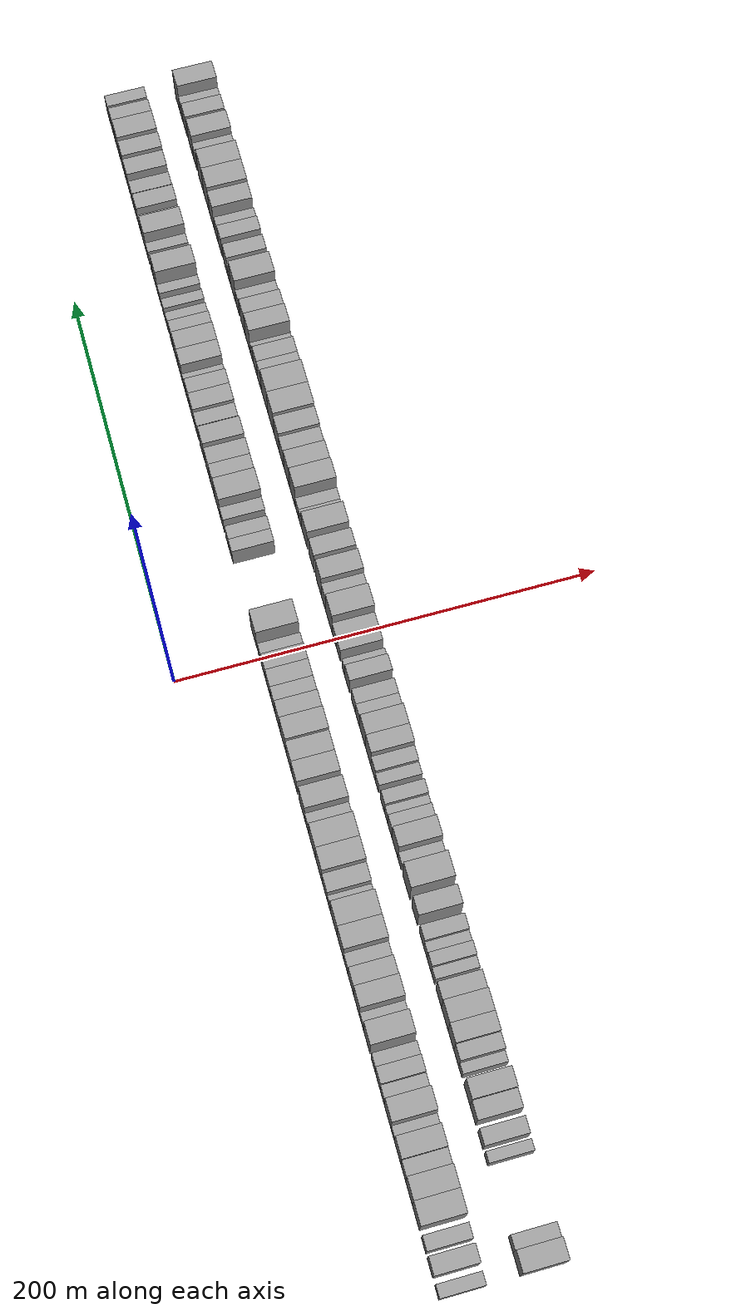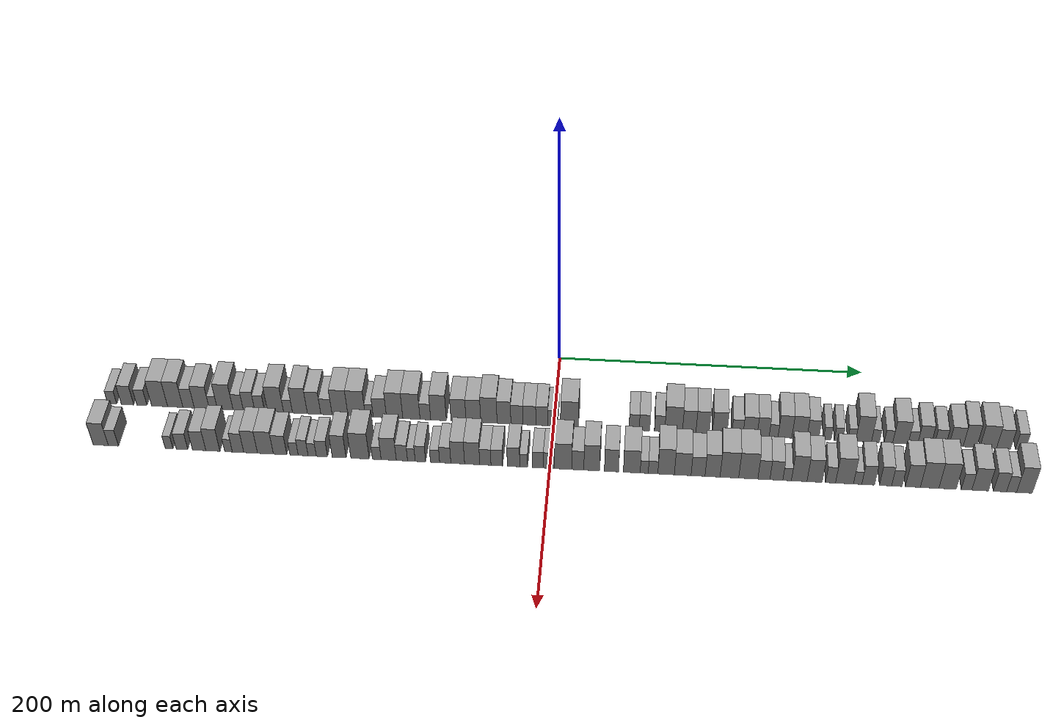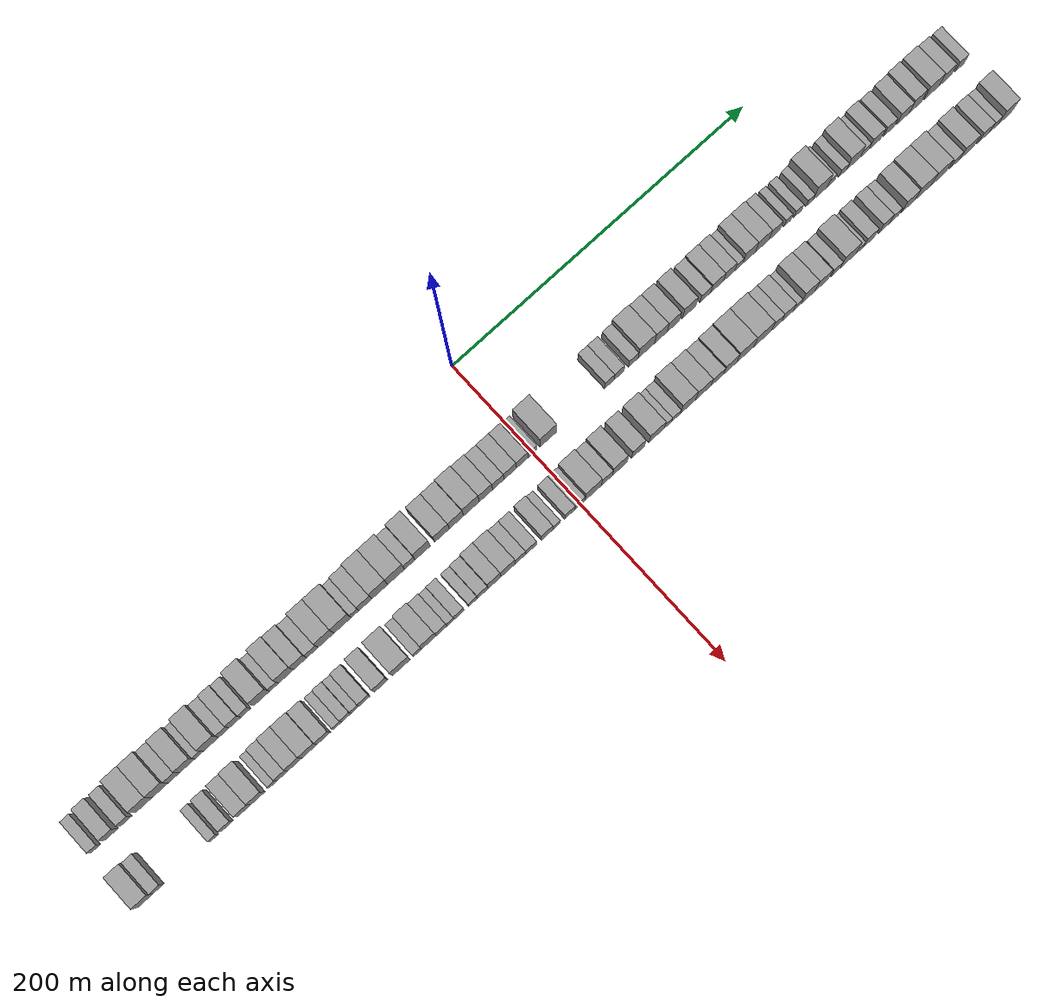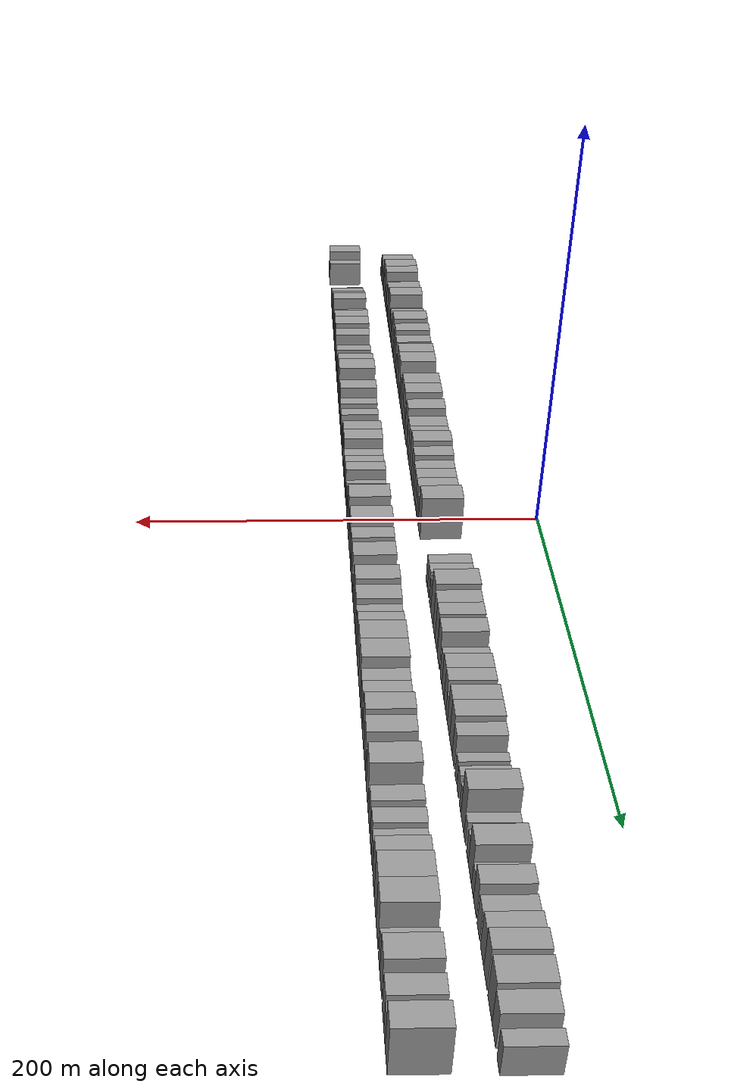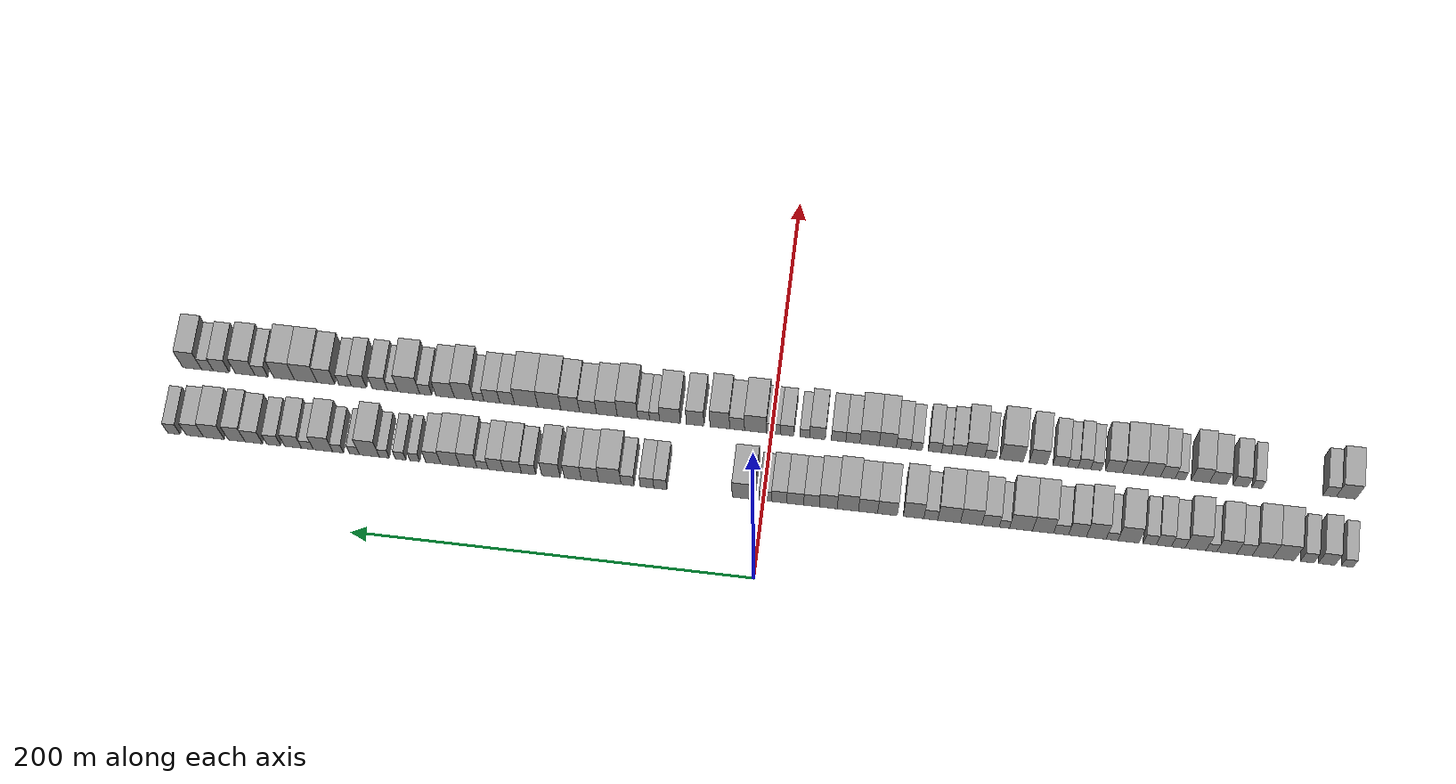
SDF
<sdf version="1.6">
 <world name="default">
  <scene>
   <sky><clouds><speed>12</speed></clouds></sky>
   <ambient>0.4 0.4 0.4 1</ambient>
   <background>0.7 0.7 0.7 1</background>
   <shadows>1</shadows>
  </scene>
  <gravity>0 0 -9.8066</gravity>
  <magnetic_field>6e-06 2.3e-05 -4.2e-05</magnetic_field>
  <physics default="0" name="default_physics" type="ode">
   <ode>
    <solver>
     <type>quick</type>
     <iters>10</iters>
     <sor>1.0</sor>
     <use_dynamic_moi_rescaling>0</use_dynamic_moi_rescaling>
    </solver>
    <constraints>
     <cfm>0</cfm>
     <erp>0.2</erp>
     <contact_max_correcting_vel>100</contact_max_correcting_vel>
     <contact_surface_layer>0.001</contact_surface_layer>
    </constraints>
   </ode>
   <max_step_size>0.004</max_step_size>
   <real_time_factor>1</real_time_factor>
   <real_time_update_rate>250</real_time_update_rate>
  </physics>
  <light name="sun" type="directional">
   <pose>0 0 10 0 0 0</pose>
   <diffuse>0.8 0.8 0.8 1</diffuse>
   <specular>0.2 0.2 0.2 1</specular>
   <attenuation>
    <range>1000</range>
    <constant>0.9</constant>
    <linear>0.01</linear>
    <quadratic>0.001</quadratic>
   </attenuation>
   <direction>-0.5 0.1 -0.9</direction>
  </light>
  <model name="building_1">
   <static>1</static>
   <pose>50.0000 -287.0523 0 0.000000 0.000000 0.000000</pose>
   <link name="link">
    <pose>0 0 6.00 0 0 0</pose>
    <collision name="collision"><geometry><box><size>20.0000 5.8953 12.0000</size></box></geometry></collision>
    <visual name="visual">
     <cast_shadows>0</cast_shadows>
     <geometry><box><size>20.0000 5.8953 12.0000</size></box></geometry>
     <material>
      <script>
       <uri>model://grey_wall/materials/scripts</uri>
       <uri>model://grey_wall/materials/textures</uri>
       <name>vrc/grey_wall</name>
      </script>
     </material>
    </visual>
   </link>
  </model>
  <model name="building_2">
   <static>1</static>
   <pose>50.0000 -277.0093 0 0.000000 0.000000 0.000000</pose>
   <link name="link">
    <pose>0 0 9.00 0 0 0</pose>
    <collision name="collision"><geometry><box><size>20.0000 8.1908 18.0000</size></box></geometry></collision>
    <visual name="visual">
     <cast_shadows>0</cast_shadows>
     <geometry><box><size>20.0000 8.1908 18.0000</size></box></geometry>
     <material>
      <script>
       <uri>model://grey_wall/materials/scripts</uri>
       <uri>model://grey_wall/materials/textures</uri>
       <name>vrc/grey_wall</name>
      </script>
     </material>
    </visual>
   </link>
  </model>
  <model name="building_3">
   <static>1</static>
   <pose>50.0000 -267.5539 0 0.000000 0.000000 0.000000</pose>
   <link name="link">
    <pose>0 0 7.50 0 0 0</pose>
    <collision name="collision"><geometry><box><size>20.0000 6.7200 15.0000</size></box></geometry></collision>
    <visual name="visual">
     <cast_shadows>0</cast_shadows>
     <geometry><box><size>20.0000 6.7200 15.0000</size></box></geometry>
     <material>
      <script>
       <uri>model://grey_wall/materials/scripts</uri>
       <uri>model://grey_wall/materials/textures</uri>
       <name>vrc/grey_wall</name>
      </script>
     </material>
    </visual>
   </link>
  </model>
  <model name="building_4">
   <static>1</static>
   <pose>50.0000 -255.9234 0 0.000000 0.000000 0.000000</pose>
   <link name="link">
    <pose>0 0 12.00 0 0 0</pose>
    <collision name="collision"><geometry><box><size>20.0000 10.5409 24.0000</size></box></geometry></collision>
    <visual name="visual">
     <cast_shadows>0</cast_shadows>
     <geometry><box><size>20.0000 10.5409 24.0000</size></box></geometry>
     <material>
      <script>
       <uri>model://grey_wall/materials/scripts</uri>
       <uri>model://grey_wall/materials/textures</uri>
       <name>vrc/grey_wall</name>
      </script>
     </material>
    </visual>
   </link>
  </model>
  <model name="building_5">
   <static>1</static>
   <pose>50.0000 -245.6184 0 0.000000 0.000000 0.000000</pose>
   <link name="link">
    <pose>0 0 12.00 0 0 0</pose>
    <collision name="collision"><geometry><box><size>20.0000 10.0692 24.0000</size></box></geometry></collision>
    <visual name="visual">
     <cast_shadows>0</cast_shadows>
     <geometry><box><size>20.0000 10.0692 24.0000</size></box></geometry>
     <material>
      <script>
       <uri>model://grey_wall/materials/scripts</uri>
       <uri>model://grey_wall/materials/textures</uri>
       <name>vrc/grey_wall</name>
      </script>
     </material>
    </visual>
   </link>
  </model>
  <model name="building_6">
   <static>1</static>
   <pose>50.0000 -236.8694 0 0.000000 0.000000 0.000000</pose>
   <link name="link">
    <pose>0 0 9.00 0 0 0</pose>
    <collision name="collision"><geometry><box><size>20.0000 7.4288 18.0000</size></box></geometry></collision>
    <visual name="visual">
     <cast_shadows>0</cast_shadows>
     <geometry><box><size>20.0000 7.4288 18.0000</size></box></geometry>
     <material>
      <script>
       <uri>model://grey_wall/materials/scripts</uri>
       <uri>model://grey_wall/materials/textures</uri>
       <name>vrc/grey_wall</name>
      </script>
     </material>
    </visual>
   </link>
  </model>
  <model name="building_7">
   <static>1</static>
   <pose>50.0000 -228.2366 0 0.000000 0.000000 0.000000</pose>
   <link name="link">
    <pose>0 0 10.50 0 0 0</pose>
    <collision name="collision"><geometry><box><size>20.0000 9.8366 21.0000</size></box></geometry></collision>
    <visual name="visual">
     <cast_shadows>0</cast_shadows>
     <geometry><box><size>20.0000 9.8366 21.0000</size></box></geometry>
     <material>
      <script>
       <uri>model://grey_wall/materials/scripts</uri>
       <uri>model://grey_wall/materials/textures</uri>
       <name>vrc/grey_wall</name>
      </script>
     </material>
    </visual>
   </link>
  </model>
  <model name="building_8">
   <static>1</static>
   <pose>50.0000 -220.6648 0 0.000000 0.000000 0.000000</pose>
   <link name="link">
    <pose>0 0 6.00 0 0 0</pose>
    <collision name="collision"><geometry><box><size>20.0000 5.3072 12.0000</size></box></geometry></collision>
    <visual name="visual">
     <cast_shadows>0</cast_shadows>
     <geometry><box><size>20.0000 5.3072 12.0000</size></box></geometry>
     <material>
      <script>
       <uri>model://grey_wall/materials/scripts</uri>
       <uri>model://grey_wall/materials/textures</uri>
       <name>vrc/grey_wall</name>
      </script>
     </material>
    </visual>
   </link>
  </model>
  <model name="building_9">
   <static>1</static>
   <pose>50.0000 -212.8576 0 0.000000 0.000000 0.000000</pose>
   <link name="link">
    <pose>0 0 12.00 0 0 0</pose>
    <collision name="collision"><geometry><box><size>20.0000 10.3071 24.0000</size></box></geometry></collision>
    <visual name="visual">
     <cast_shadows>0</cast_shadows>
     <geometry><box><size>20.0000 10.3071 24.0000</size></box></geometry>
     <material>
      <script>
       <uri>model://grey_wall/materials/scripts</uri>
       <uri>model://grey_wall/materials/textures</uri>
       <name>vrc/grey_wall</name>
      </script>
     </material>
    </visual>
   </link>
  </model>
  <model name="building_10">
   <static>1</static>
   <pose>50.0000 -204.3506 0 0.000000 0.000000 0.000000</pose>
   <link name="link">
    <pose>0 0 7.50 0 0 0</pose>
    <collision name="collision"><geometry><box><size>20.0000 6.7071 15.0000</size></box></geometry></collision>
    <visual name="visual">
     <cast_shadows>0</cast_shadows>
     <geometry><box><size>20.0000 6.7071 15.0000</size></box></geometry>
     <material>
      <script>
       <uri>model://grey_wall/materials/scripts</uri>
       <uri>model://grey_wall/materials/textures</uri>
       <name>vrc/grey_wall</name>
      </script>
     </material>
    </visual>
   </link>
  </model>
  <model name="building_11">
   <static>1</static>
   <pose>50.0000 -197.2316 0 0.000000 0.000000 0.000000</pose>
   <link name="link">
    <pose>0 0 9.00 0 0 0</pose>
    <collision name="collision"><geometry><box><size>20.0000 7.5308 18.0000</size></box></geometry></collision>
    <visual name="visual">
     <cast_shadows>0</cast_shadows>
     <geometry><box><size>20.0000 7.5308 18.0000</size></box></geometry>
     <material>
      <script>
       <uri>model://grey_wall/materials/scripts</uri>
       <uri>model://grey_wall/materials/textures</uri>
       <name>vrc/grey_wall</name>
      </script>
     </material>
    </visual>
   </link>
  </model>
  <model name="building_12">
   <static>1</static>
   <pose>50.0000 -190.2864 0 0.000000 0.000000 0.000000</pose>
   <link name="link">
    <pose>0 0 7.50 0 0 0</pose>
    <collision name="collision"><geometry><box><size>20.0000 6.3596 15.0000</size></box></geometry></collision>
    <visual name="visual">
     <cast_shadows>0</cast_shadows>
     <geometry><box><size>20.0000 6.3596 15.0000</size></box></geometry>
     <material>
      <script>
       <uri>model://grey_wall/materials/scripts</uri>
       <uri>model://grey_wall/materials/textures</uri>
       <name>vrc/grey_wall</name>
      </script>
     </material>
    </visual>
   </link>
  </model>
  <model name="building_13">
   <static>1</static>
   <pose>50.0000 -179.9060 0 0.000000 0.000000 0.000000</pose>
   <link name="link">
    <pose>0 0 12.00 0 0 0</pose>
    <collision name="collision"><geometry><box><size>20.0000 10.4011 24.0000</size></box></geometry></collision>
    <visual name="visual">
     <cast_shadows>0</cast_shadows>
     <geometry><box><size>20.0000 10.4011 24.0000</size></box></geometry>
     <material>
      <script>
       <uri>model://grey_wall/materials/scripts</uri>
       <uri>model://grey_wall/materials/textures</uri>
       <name>vrc/grey_wall</name>
      </script>
     </material>
    </visual>
   </link>
  </model>
  <model name="building_14">
   <static>1</static>
   <pose>50.0000 -171.7986 0 0.000000 0.000000 0.000000</pose>
   <link name="link">
    <pose>0 0 6.00 0 0 0</pose>
    <collision name="collision"><geometry><box><size>20.0000 5.8136 12.0000</size></box></geometry></collision>
    <visual name="visual">
     <cast_shadows>0</cast_shadows>
     <geometry><box><size>20.0000 5.8136 12.0000</size></box></geometry>
     <material>
      <script>
       <uri>model://grey_wall/materials/scripts</uri>
       <uri>model://grey_wall/materials/textures</uri>
       <name>vrc/grey_wall</name>
      </script>
     </material>
    </visual>
   </link>
  </model>
  <model name="building_15">
   <static>1</static>
   <pose>50.0000 -164.0420 0 0.000000 0.000000 0.000000</pose>
   <link name="link">
    <pose>0 0 12.00 0 0 0</pose>
    <collision name="collision"><geometry><box><size>20.0000 9.6997 24.0000</size></box></geometry></collision>
    <visual name="visual">
     <cast_shadows>0</cast_shadows>
     <geometry><box><size>20.0000 9.6997 24.0000</size></box></geometry>
     <material>
      <script>
       <uri>model://grey_wall/materials/scripts</uri>
       <uri>model://grey_wall/materials/textures</uri>
       <name>vrc/grey_wall</name>
      </script>
     </material>
    </visual>
   </link>
  </model>
  <model name="building_16">
   <static>1</static>
   <pose>50.0000 -154.8154 0 0.000000 0.000000 0.000000</pose>
   <link name="link">
    <pose>0 0 10.50 0 0 0</pose>
    <collision name="collision"><geometry><box><size>20.0000 8.7535 21.0000</size></box></geometry></collision>
    <visual name="visual">
     <cast_shadows>0</cast_shadows>
     <geometry><box><size>20.0000 8.7535 21.0000</size></box></geometry>
     <material>
      <script>
       <uri>model://grey_wall/materials/scripts</uri>
       <uri>model://grey_wall/materials/textures</uri>
       <name>vrc/grey_wall</name>
      </script>
     </material>
    </visual>
   </link>
  </model>
  <model name="building_17">
   <static>1</static>
   <pose>50.0000 -146.7566 0 0.000000 0.000000 0.000000</pose>
   <link name="link">
    <pose>0 0 7.50 0 0 0</pose>
    <collision name="collision"><geometry><box><size>20.0000 7.3642 15.0000</size></box></geometry></collision>
    <visual name="visual">
     <cast_shadows>0</cast_shadows>
     <geometry><box><size>20.0000 7.3642 15.0000</size></box></geometry>
     <material>
      <script>
       <uri>model://grey_wall/materials/scripts</uri>
       <uri>model://grey_wall/materials/textures</uri>
       <name>vrc/grey_wall</name>
      </script>
     </material>
    </visual>
   </link>
  </model>
  <model name="building_18">
   <static>1</static>
   <pose>50.0000 -137.8988 0 0.000000 0.000000 0.000000</pose>
   <link name="link">
    <pose>0 0 12.00 0 0 0</pose>
    <collision name="collision"><geometry><box><size>20.0000 10.3513 24.0000</size></box></geometry></collision>
    <visual name="visual">
     <cast_shadows>0</cast_shadows>
     <geometry><box><size>20.0000 10.3513 24.0000</size></box></geometry>
     <material>
      <script>
       <uri>model://grey_wall/materials/scripts</uri>
       <uri>model://grey_wall/materials/textures</uri>
       <name>vrc/grey_wall</name>
      </script>
     </material>
    </visual>
   </link>
  </model>
  <model name="building_19">
   <static>1</static>
   <pose>50.0000 -127.0697 0 0.000000 0.000000 0.000000</pose>
   <link name="link">
    <pose>0 0 12.00 0 0 0</pose>
    <collision name="collision"><geometry><box><size>20.0000 11.3070 24.0000</size></box></geometry></collision>
    <visual name="visual">
     <cast_shadows>0</cast_shadows>
     <geometry><box><size>20.0000 11.3070 24.0000</size></box></geometry>
     <material>
      <script>
       <uri>model://grey_wall/materials/scripts</uri>
       <uri>model://grey_wall/materials/textures</uri>
       <name>vrc/grey_wall</name>
      </script>
     </material>
    </visual>
   </link>
  </model>
  <model name="building_20">
   <static>1</static>
   <pose>50.0000 -118.8807 0 0.000000 0.000000 0.000000</pose>
   <link name="link">
    <pose>0 0 6.00 0 0 0</pose>
    <collision name="collision"><geometry><box><size>20.0000 5.0709 12.0000</size></box></geometry></collision>
    <visual name="visual">
     <cast_shadows>0</cast_shadows>
     <geometry><box><size>20.0000 5.0709 12.0000</size></box></geometry>
     <material>
      <script>
       <uri>model://grey_wall/materials/scripts</uri>
       <uri>model://grey_wall/materials/textures</uri>
       <name>vrc/grey_wall</name>
      </script>
     </material>
    </visual>
   </link>
  </model>
  <model name="building_21">
   <static>1</static>
   <pose>50.0000 -112.0234 0 0.000000 0.000000 0.000000</pose>
   <link name="link">
    <pose>0 0 9.00 0 0 0</pose>
    <collision name="collision"><geometry><box><size>20.0000 8.6437 18.0000</size></box></geometry></collision>
    <visual name="visual">
     <cast_shadows>0</cast_shadows>
     <geometry><box><size>20.0000 8.6437 18.0000</size></box></geometry>
     <material>
      <script>
       <uri>model://grey_wall/materials/scripts</uri>
       <uri>model://grey_wall/materials/textures</uri>
       <name>vrc/grey_wall</name>
      </script>
     </material>
    </visual>
   </link>
  </model>
  <model name="building_22">
   <static>1</static>
   <pose>50.0000 -102.4219 0 0.000000 0.000000 0.000000</pose>
   <link name="link">
    <pose>0 0 12.00 0 0 0</pose>
    <collision name="collision"><geometry><box><size>20.0000 10.5594 24.0000</size></box></geometry></collision>
    <visual name="visual">
     <cast_shadows>0</cast_shadows>
     <geometry><box><size>20.0000 10.5594 24.0000</size></box></geometry>
     <material>
      <script>
       <uri>model://grey_wall/materials/scripts</uri>
       <uri>model://grey_wall/materials/textures</uri>
       <name>vrc/grey_wall</name>
      </script>
     </material>
    </visual>
   </link>
  </model>
  <model name="building_23">
   <static>1</static>
   <pose>50.0000 -91.5550 0 0.000000 0.000000 0.000000</pose>
   <link name="link">
    <pose>0 0 12.00 0 0 0</pose>
    <collision name="collision"><geometry><box><size>20.0000 11.1743 24.0000</size></box></geometry></collision>
    <visual name="visual">
     <cast_shadows>0</cast_shadows>
     <geometry><box><size>20.0000 11.1743 24.0000</size></box></geometry>
     <material>
      <script>
       <uri>model://grey_wall/materials/scripts</uri>
       <uri>model://grey_wall/materials/textures</uri>
       <name>vrc/grey_wall</name>
      </script>
     </material>
    </visual>
   </link>
  </model>
  <model name="building_24">
   <static>1</static>
   <pose>50.0000 -82.5358 0 0.000000 0.000000 0.000000</pose>
   <link name="link">
    <pose>0 0 7.50 0 0 0</pose>
    <collision name="collision"><geometry><box><size>20.0000 6.8641 15.0000</size></box></geometry></collision>
    <visual name="visual">
     <cast_shadows>0</cast_shadows>
     <geometry><box><size>20.0000 6.8641 15.0000</size></box></geometry>
     <material>
      <script>
       <uri>model://grey_wall/materials/scripts</uri>
       <uri>model://grey_wall/materials/textures</uri>
       <name>vrc/grey_wall</name>
      </script>
     </material>
    </visual>
   </link>
  </model>
  <model name="building_25">
   <static>1</static>
   <pose>50.0000 -74.0239 0 0.000000 0.000000 0.000000</pose>
   <link name="link">
    <pose>0 0 12.00 0 0 0</pose>
    <collision name="collision"><geometry><box><size>20.0000 10.1597 24.0000</size></box></geometry></collision>
    <visual name="visual">
     <cast_shadows>0</cast_shadows>
     <geometry><box><size>20.0000 10.1597 24.0000</size></box></geometry>
     <material>
      <script>
       <uri>model://grey_wall/materials/scripts</uri>
       <uri>model://grey_wall/materials/textures</uri>
       <name>vrc/grey_wall</name>
      </script>
     </material>
    </visual>
   </link>
  </model>
  <model name="building_26">
   <static>1</static>
   <pose>50.0000 -61.0833 0 0.000000 0.000000 0.000000</pose>
   <link name="link">
    <pose>0 0 10.50 0 0 0</pose>
    <collision name="collision"><geometry><box><size>20.0000 9.7216 21.0000</size></box></geometry></collision>
    <visual name="visual">
     <cast_shadows>0</cast_shadows>
     <geometry><box><size>20.0000 9.7216 21.0000</size></box></geometry>
     <material>
      <script>
       <uri>model://grey_wall/materials/scripts</uri>
       <uri>model://grey_wall/materials/textures</uri>
       <name>vrc/grey_wall</name>
      </script>
     </material>
    </visual>
   </link>
  </model>
  <model name="building_27">
   <static>1</static>
   <pose>50.0000 -51.4662 0 0.000000 0.000000 0.000000</pose>
   <link name="link">
    <pose>0 0 10.50 0 0 0</pose>
    <collision name="collision"><geometry><box><size>20.0000 9.5127 21.0000</size></box></geometry></collision>
    <visual name="visual">
     <cast_shadows>0</cast_shadows>
     <geometry><box><size>20.0000 9.5127 21.0000</size></box></geometry>
     <material>
      <script>
       <uri>model://grey_wall/materials/scripts</uri>
       <uri>model://grey_wall/materials/textures</uri>
       <name>vrc/grey_wall</name>
      </script>
     </material>
    </visual>
   </link>
  </model>
  <model name="building_28">
   <static>1</static>
   <pose>50.0000 -41.4690 0 0.000000 0.000000 0.000000</pose>
   <link name="link">
    <pose>0 0 12.00 0 0 0</pose>
    <collision name="collision"><geometry><box><size>20.0000 10.4816 24.0000</size></box></geometry></collision>
    <visual name="visual">
     <cast_shadows>0</cast_shadows>
     <geometry><box><size>20.0000 10.4816 24.0000</size></box></geometry>
     <material>
      <script>
       <uri>model://grey_wall/materials/scripts</uri>
       <uri>model://grey_wall/materials/textures</uri>
       <name>vrc/grey_wall</name>
      </script>
     </material>
    </visual>
   </link>
  </model>
  <model name="building_29">
   <static>1</static>
   <pose>50.0000 -31.7760 0 0.000000 0.000000 0.000000</pose>
   <link name="link">
    <pose>0 0 10.50 0 0 0</pose>
    <collision name="collision"><geometry><box><size>20.0000 8.9044 21.0000</size></box></geometry></collision>
    <visual name="visual">
     <cast_shadows>0</cast_shadows>
     <geometry><box><size>20.0000 8.9044 21.0000</size></box></geometry>
     <material>
      <script>
       <uri>model://grey_wall/materials/scripts</uri>
       <uri>model://grey_wall/materials/textures</uri>
       <name>vrc/grey_wall</name>
      </script>
     </material>
    </visual>
   </link>
  </model>
  <model name="building_30">
   <static>1</static>
   <pose>50.0000 -23.4686 0 0.000000 0.000000 0.000000</pose>
   <link name="link">
    <pose>0 0 9.00 0 0 0</pose>
    <collision name="collision"><geometry><box><size>20.0000 7.7102 18.0000</size></box></geometry></collision>
    <visual name="visual">
     <cast_shadows>0</cast_shadows>
     <geometry><box><size>20.0000 7.7102 18.0000</size></box></geometry>
     <material>
      <script>
       <uri>model://grey_wall/materials/scripts</uri>
       <uri>model://grey_wall/materials/textures</uri>
       <name>vrc/grey_wall</name>
      </script>
     </material>
    </visual>
   </link>
  </model>
  <model name="building_31">
   <static>1</static>
   <pose>50.0000 -15.4387 0 0.000000 0.000000 0.000000</pose>
   <link name="link">
    <pose>0 0 9.00 0 0 0</pose>
    <collision name="collision"><geometry><box><size>20.0000 8.3496 18.0000</size></box></geometry></collision>
    <visual name="visual">
     <cast_shadows>0</cast_shadows>
     <geometry><box><size>20.0000 8.3496 18.0000</size></box></geometry>
     <material>
      <script>
       <uri>model://grey_wall/materials/scripts</uri>
       <uri>model://grey_wall/materials/textures</uri>
       <name>vrc/grey_wall</name>
      </script>
     </material>
    </visual>
   </link>
  </model>
  <model name="building_32">
   <static>1</static>
   <pose>50.0000 -7.4172 0 0.000000 0.000000 0.000000</pose>
   <link name="link">
    <pose>0 0 9.00 0 0 0</pose>
    <collision name="collision"><geometry><box><size>20.0000 7.6935 18.0000</size></box></geometry></collision>
    <visual name="visual">
     <cast_shadows>0</cast_shadows>
     <geometry><box><size>20.0000 7.6935 18.0000</size></box></geometry>
     <material>
      <script>
       <uri>model://grey_wall/materials/scripts</uri>
       <uri>model://grey_wall/materials/textures</uri>
       <name>vrc/grey_wall</name>
      </script>
     </material>
    </visual>
   </link>
  </model>
  <model name="building_33">
   <static>1</static>
   <pose>50.0000 -0.4919 0 0.000000 0.000000 0.000000</pose>
   <link name="link">
    <pose>0 0 7.50 0 0 0</pose>
    <collision name="collision"><geometry><box><size>20.0000 6.1572 15.0000</size></box></geometry></collision>
    <visual name="visual">
     <cast_shadows>0</cast_shadows>
     <geometry><box><size>20.0000 6.1572 15.0000</size></box></geometry>
     <material>
      <script>
       <uri>model://grey_wall/materials/scripts</uri>
       <uri>model://grey_wall/materials/textures</uri>
       <name>vrc/grey_wall</name>
      </script>
     </material>
    </visual>
   </link>
  </model>
  <model name="building_34">
   <static>1</static>
   <pose>50.0000 10.2601 0 0.000000 0.000000 0.000000</pose>
   <link name="link">
    <pose>0 0 12.00 0 0 0</pose>
    <collision name="collision"><geometry><box><size>20.0000 11.3468 24.0000</size></box></geometry></collision>
    <visual name="visual">
     <cast_shadows>0</cast_shadows>
     <geometry><box><size>20.0000 11.3468 24.0000</size></box></geometry>
     <material>
      <script>
       <uri>model://grey_wall/materials/scripts</uri>
       <uri>model://grey_wall/materials/textures</uri>
       <name>vrc/grey_wall</name>
      </script>
     </material>
    </visual>
   </link>
  </model>
  <model name="building_35">
   <static>1</static>
   <pose>50.0000 51.6948 0 0.000000 0.000000 0.000000</pose>
   <link name="link">
    <pose>0 0 7.50 0 0 0</pose>
    <collision name="collision"><geometry><box><size>20.0000 6.5075 15.0000</size></box></geometry></collision>
    <visual name="visual">
     <cast_shadows>0</cast_shadows>
     <geometry><box><size>20.0000 6.5075 15.0000</size></box></geometry>
     <material>
      <script>
       <uri>model://grey_wall/materials/scripts</uri>
       <uri>model://grey_wall/materials/textures</uri>
       <name>vrc/grey_wall</name>
      </script>
     </material>
    </visual>
   </link>
  </model>
  <model name="building_36">
   <static>1</static>
   <pose>50.0000 58.3173 0 0.000000 0.000000 0.000000</pose>
   <link name="link">
    <pose>0 0 7.50 0 0 0</pose>
    <collision name="collision"><geometry><box><size>20.0000 6.7374 15.0000</size></box></geometry></collision>
    <visual name="visual">
     <cast_shadows>0</cast_shadows>
     <geometry><box><size>20.0000 6.7374 15.0000</size></box></geometry>
     <material>
      <script>
       <uri>model://grey_wall/materials/scripts</uri>
       <uri>model://grey_wall/materials/textures</uri>
       <name>vrc/grey_wall</name>
      </script>
     </material>
    </visual>
   </link>
  </model>
  <model name="building_37">
   <static>1</static>
   <pose>50.0000 67.9673 0 0.000000 0.000000 0.000000</pose>
   <link name="link">
    <pose>0 0 7.50 0 0 0</pose>
    <collision name="collision"><geometry><box><size>20.0000 6.5625 15.0000</size></box></geometry></collision>
    <visual name="visual">
     <cast_shadows>0</cast_shadows>
     <geometry><box><size>20.0000 6.5625 15.0000</size></box></geometry>
     <material>
      <script>
       <uri>model://grey_wall/materials/scripts</uri>
       <uri>model://grey_wall/materials/textures</uri>
       <name>vrc/grey_wall</name>
      </script>
     </material>
    </visual>
   </link>
  </model>
  <model name="building_38">
   <static>1</static>
   <pose>50.0000 76.8623 0 0.000000 0.000000 0.000000</pose>
   <link name="link">
    <pose>0 0 12.00 0 0 0</pose>
    <collision name="collision"><geometry><box><size>20.0000 11.2276 24.0000</size></box></geometry></collision>
    <visual name="visual">
     <cast_shadows>0</cast_shadows>
     <geometry><box><size>20.0000 11.2276 24.0000</size></box></geometry>
     <material>
      <script>
       <uri>model://grey_wall/materials/scripts</uri>
       <uri>model://grey_wall/materials/textures</uri>
       <name>vrc/grey_wall</name>
      </script>
     </material>
    </visual>
   </link>
  </model>
  <model name="building_39">
   <static>1</static>
   <pose>50.0000 86.7764 0 0.000000 0.000000 0.000000</pose>
   <link name="link">
    <pose>0 0 10.50 0 0 0</pose>
    <collision name="collision"><geometry><box><size>20.0000 8.6006 21.0000</size></box></geometry></collision>
    <visual name="visual">
     <cast_shadows>0</cast_shadows>
     <geometry><box><size>20.0000 8.6006 21.0000</size></box></geometry>
     <material>
      <script>
       <uri>model://grey_wall/materials/scripts</uri>
       <uri>model://grey_wall/materials/textures</uri>
       <name>vrc/grey_wall</name>
      </script>
     </material>
    </visual>
   </link>
  </model>
  <model name="building_40">
   <static>1</static>
   <pose>50.0000 95.3195 0 0.000000 0.000000 0.000000</pose>
   <link name="link">
    <pose>0 0 10.50 0 0 0</pose>
    <collision name="collision"><geometry><box><size>20.0000 8.4856 21.0000</size></box></geometry></collision>
    <visual name="visual">
     <cast_shadows>0</cast_shadows>
     <geometry><box><size>20.0000 8.4856 21.0000</size></box></geometry>
     <material>
      <script>
       <uri>model://grey_wall/materials/scripts</uri>
       <uri>model://grey_wall/materials/textures</uri>
       <name>vrc/grey_wall</name>
      </script>
     </material>
    </visual>
   </link>
  </model>
  <model name="building_41">
   <static>1</static>
   <pose>50.0000 106.1843 0 0.000000 0.000000 0.000000</pose>
   <link name="link">
    <pose>0 0 10.50 0 0 0</pose>
    <collision name="collision"><geometry><box><size>20.0000 9.2440 21.0000</size></box></geometry></collision>
    <visual name="visual">
     <cast_shadows>0</cast_shadows>
     <geometry><box><size>20.0000 9.2440 21.0000</size></box></geometry>
     <material>
      <script>
       <uri>model://grey_wall/materials/scripts</uri>
       <uri>model://grey_wall/materials/textures</uri>
       <name>vrc/grey_wall</name>
      </script>
     </material>
    </visual>
   </link>
  </model>
  <model name="building_42">
   <static>1</static>
   <pose>50.0000 117.4076 0 0.000000 0.000000 0.000000</pose>
   <link name="link">
    <pose>0 0 7.50 0 0 0</pose>
    <collision name="collision"><geometry><box><size>20.0000 7.2025 15.0000</size></box></geometry></collision>
    <visual name="visual">
     <cast_shadows>0</cast_shadows>
     <geometry><box><size>20.0000 7.2025 15.0000</size></box></geometry>
     <material>
      <script>
       <uri>model://grey_wall/materials/scripts</uri>
       <uri>model://grey_wall/materials/textures</uri>
       <name>vrc/grey_wall</name>
      </script>
     </material>
    </visual>
   </link>
  </model>
  <model name="building_43">
   <static>1</static>
   <pose>50.0000 125.4873 0 0.000000 0.000000 0.000000</pose>
   <link name="link">
    <pose>0 0 9.00 0 0 0</pose>
    <collision name="collision"><geometry><box><size>20.0000 8.9569 18.0000</size></box></geometry></collision>
    <visual name="visual">
     <cast_shadows>0</cast_shadows>
     <geometry><box><size>20.0000 8.9569 18.0000</size></box></geometry>
     <material>
      <script>
       <uri>model://grey_wall/materials/scripts</uri>
       <uri>model://grey_wall/materials/textures</uri>
       <name>vrc/grey_wall</name>
      </script>
     </material>
    </visual>
   </link>
  </model>
  <model name="building_44">
   <static>1</static>
   <pose>50.0000 133.7983 0 0.000000 0.000000 0.000000</pose>
   <link name="link">
    <pose>0 0 9.00 0 0 0</pose>
    <collision name="collision"><geometry><box><size>20.0000 7.6651 18.0000</size></box></geometry></collision>
    <visual name="visual">
     <cast_shadows>0</cast_shadows>
     <geometry><box><size>20.0000 7.6651 18.0000</size></box></geometry>
     <material>
      <script>
       <uri>model://grey_wall/materials/scripts</uri>
       <uri>model://grey_wall/materials/textures</uri>
       <name>vrc/grey_wall</name>
      </script>
     </material>
    </visual>
   </link>
  </model>
  <model name="building_45">
   <static>1</static>
   <pose>50.0000 140.4432 0 0.000000 0.000000 0.000000</pose>
   <link name="link">
    <pose>0 0 6.00 0 0 0</pose>
    <collision name="collision"><geometry><box><size>20.0000 5.6247 12.0000</size></box></geometry></collision>
    <visual name="visual">
     <cast_shadows>0</cast_shadows>
     <geometry><box><size>20.0000 5.6247 12.0000</size></box></geometry>
     <material>
      <script>
       <uri>model://grey_wall/materials/scripts</uri>
       <uri>model://grey_wall/materials/textures</uri>
       <name>vrc/grey_wall</name>
      </script>
     </material>
    </visual>
   </link>
  </model>
  <model name="building_46">
   <static>1</static>
   <pose>50.0000 147.6350 0 0.000000 0.000000 0.000000</pose>
   <link name="link">
    <pose>0 0 10.50 0 0 0</pose>
    <collision name="collision"><geometry><box><size>20.0000 8.7589 21.0000</size></box></geometry></collision>
    <visual name="visual">
     <cast_shadows>0</cast_shadows>
     <geometry><box><size>20.0000 8.7589 21.0000</size></box></geometry>
     <material>
      <script>
       <uri>model://grey_wall/materials/scripts</uri>
       <uri>model://grey_wall/materials/textures</uri>
       <name>vrc/grey_wall</name>
      </script>
     </material>
    </visual>
   </link>
  </model>
  <model name="building_47">
   <static>1</static>
   <pose>50.0000 156.7468 0 0.000000 0.000000 0.000000</pose>
   <link name="link">
    <pose>0 0 10.50 0 0 0</pose>
    <collision name="collision"><geometry><box><size>20.0000 9.4646 21.0000</size></box></geometry></collision>
    <visual name="visual">
     <cast_shadows>0</cast_shadows>
     <geometry><box><size>20.0000 9.4646 21.0000</size></box></geometry>
     <material>
      <script>
       <uri>model://grey_wall/materials/scripts</uri>
       <uri>model://grey_wall/materials/textures</uri>
       <name>vrc/grey_wall</name>
      </script>
     </material>
    </visual>
   </link>
  </model>
  <model name="building_48">
   <static>1</static>
   <pose>50.0000 165.2521 0 0.000000 0.000000 0.000000</pose>
   <link name="link">
    <pose>0 0 9.00 0 0 0</pose>
    <collision name="collision"><geometry><box><size>20.0000 7.5461 18.0000</size></box></geometry></collision>
    <visual name="visual">
     <cast_shadows>0</cast_shadows>
     <geometry><box><size>20.0000 7.5461 18.0000</size></box></geometry>
     <material>
      <script>
       <uri>model://grey_wall/materials/scripts</uri>
       <uri>model://grey_wall/materials/textures</uri>
       <name>vrc/grey_wall</name>
      </script>
     </material>
    </visual>
   </link>
  </model>
  <model name="building_49">
   <static>1</static>
   <pose>50.0000 174.4835 0 0.000000 0.000000 0.000000</pose>
   <link name="link">
    <pose>0 0 6.00 0 0 0</pose>
    <collision name="collision"><geometry><box><size>20.0000 4.9166 12.0000</size></box></geometry></collision>
    <visual name="visual">
     <cast_shadows>0</cast_shadows>
     <geometry><box><size>20.0000 4.9166 12.0000</size></box></geometry>
     <material>
      <script>
       <uri>model://grey_wall/materials/scripts</uri>
       <uri>model://grey_wall/materials/textures</uri>
       <name>vrc/grey_wall</name>
      </script>
     </material>
    </visual>
   </link>
  </model>
  <model name="building_50">
   <static>1</static>
   <pose>50.0000 181.6245 0 0.000000 0.000000 0.000000</pose>
   <link name="link">
    <pose>0 0 6.00 0 0 0</pose>
    <collision name="collision"><geometry><box><size>20.0000 5.3654 12.0000</size></box></geometry></collision>
    <visual name="visual">
     <cast_shadows>0</cast_shadows>
     <geometry><box><size>20.0000 5.3654 12.0000</size></box></geometry>
     <material>
      <script>
       <uri>model://grey_wall/materials/scripts</uri>
       <uri>model://grey_wall/materials/textures</uri>
       <name>vrc/grey_wall</name>
      </script>
     </material>
    </visual>
   </link>
  </model>
  <model name="building_51">
   <static>1</static>
   <pose>50.0000 189.8150 0 0.000000 0.000000 0.000000</pose>
   <link name="link">
    <pose>0 0 6.00 0 0 0</pose>
    <collision name="collision"><geometry><box><size>20.0000 5.0157 12.0000</size></box></geometry></collision>
    <visual name="visual">
     <cast_shadows>0</cast_shadows>
     <geometry><box><size>20.0000 5.0157 12.0000</size></box></geometry>
     <material>
      <script>
       <uri>model://grey_wall/materials/scripts</uri>
       <uri>model://grey_wall/materials/textures</uri>
       <name>vrc/grey_wall</name>
      </script>
     </material>
    </visual>
   </link>
  </model>
  <model name="building_52">
   <static>1</static>
   <pose>50.0000 197.3349 0 0.000000 0.000000 0.000000</pose>
   <link name="link">
    <pose>0 0 12.00 0 0 0</pose>
    <collision name="collision"><geometry><box><size>20.0000 10.0241 24.0000</size></box></geometry></collision>
    <visual name="visual">
     <cast_shadows>0</cast_shadows>
     <geometry><box><size>20.0000 10.0241 24.0000</size></box></geometry>
     <material>
      <script>
       <uri>model://grey_wall/materials/scripts</uri>
       <uri>model://grey_wall/materials/textures</uri>
       <name>vrc/grey_wall</name>
      </script>
     </material>
    </visual>
   </link>
  </model>
  <model name="building_53">
   <static>1</static>
   <pose>50.0000 204.8738 0 0.000000 0.000000 0.000000</pose>
   <link name="link">
    <pose>0 0 6.00 0 0 0</pose>
    <collision name="collision"><geometry><box><size>20.0000 5.0537 12.0000</size></box></geometry></collision>
    <visual name="visual">
     <cast_shadows>0</cast_shadows>
     <geometry><box><size>20.0000 5.0537 12.0000</size></box></geometry>
     <material>
      <script>
       <uri>model://grey_wall/materials/scripts</uri>
       <uri>model://grey_wall/materials/textures</uri>
       <name>vrc/grey_wall</name>
      </script>
     </material>
    </visual>
   </link>
  </model>
  <model name="building_54">
   <static>1</static>
   <pose>50.0000 213.0801 0 0.000000 0.000000 0.000000</pose>
   <link name="link">
    <pose>0 0 6.00 0 0 0</pose>
    <collision name="collision"><geometry><box><size>20.0000 5.3588 12.0000</size></box></geometry></collision>
    <visual name="visual">
     <cast_shadows>0</cast_shadows>
     <geometry><box><size>20.0000 5.3588 12.0000</size></box></geometry>
     <material>
      <script>
       <uri>model://grey_wall/materials/scripts</uri>
       <uri>model://grey_wall/materials/textures</uri>
       <name>vrc/grey_wall</name>
      </script>
     </material>
    </visual>
   </link>
  </model>
  <model name="building_55">
   <static>1</static>
   <pose>50.0000 220.6595 0 0.000000 0.000000 0.000000</pose>
   <link name="link">
    <pose>0 0 10.50 0 0 0</pose>
    <collision name="collision"><geometry><box><size>20.0000 9.8001 21.0000</size></box></geometry></collision>
    <visual name="visual">
     <cast_shadows>0</cast_shadows>
     <geometry><box><size>20.0000 9.8001 21.0000</size></box></geometry>
     <material>
      <script>
       <uri>model://grey_wall/materials/scripts</uri>
       <uri>model://grey_wall/materials/textures</uri>
       <name>vrc/grey_wall</name>
      </script>
     </material>
    </visual>
   </link>
  </model>
  <model name="building_56">
   <static>1</static>
   <pose>50.0000 228.5234 0 0.000000 0.000000 0.000000</pose>
   <link name="link">
    <pose>0 0 6.00 0 0 0</pose>
    <collision name="collision"><geometry><box><size>20.0000 5.9277 12.0000</size></box></geometry></collision>
    <visual name="visual">
     <cast_shadows>0</cast_shadows>
     <geometry><box><size>20.0000 5.9277 12.0000</size></box></geometry>
     <material>
      <script>
       <uri>model://grey_wall/materials/scripts</uri>
       <uri>model://grey_wall/materials/textures</uri>
       <name>vrc/grey_wall</name>
      </script>
     </material>
    </visual>
   </link>
  </model>
  <model name="building_57">
   <static>1</static>
   <pose>50.0000 235.7354 0 0.000000 0.000000 0.000000</pose>
   <link name="link">
    <pose>0 0 9.00 0 0 0</pose>
    <collision name="collision"><geometry><box><size>20.0000 8.4964 18.0000</size></box></geometry></collision>
    <visual name="visual">
     <cast_shadows>0</cast_shadows>
     <geometry><box><size>20.0000 8.4964 18.0000</size></box></geometry>
     <material>
      <script>
       <uri>model://grey_wall/materials/scripts</uri>
       <uri>model://grey_wall/materials/textures</uri>
       <name>vrc/grey_wall</name>
      </script>
     </material>
    </visual>
   </link>
  </model>
  <model name="building_58">
   <static>1</static>
   <pose>50.0000 245.5716 0 0.000000 0.000000 0.000000</pose>
   <link name="link">
    <pose>0 0 7.50 0 0 0</pose>
    <collision name="collision"><geometry><box><size>20.0000 7.1761 15.0000</size></box></geometry></collision>
    <visual name="visual">
     <cast_shadows>0</cast_shadows>
     <geometry><box><size>20.0000 7.1761 15.0000</size></box></geometry>
     <material>
      <script>
       <uri>model://grey_wall/materials/scripts</uri>
       <uri>model://grey_wall/materials/textures</uri>
       <name>vrc/grey_wall</name>
      </script>
     </material>
    </visual>
   </link>
  </model>
  <model name="building_59">
   <static>1</static>
   <pose>50.0000 255.5906 0 0.000000 0.000000 0.000000</pose>
   <link name="link">
    <pose>0 0 9.00 0 0 0</pose>
    <collision name="collision"><geometry><box><size>20.0000 8.8619 18.0000</size></box></geometry></collision>
    <visual name="visual">
     <cast_shadows>0</cast_shadows>
     <geometry><box><size>20.0000 8.8619 18.0000</size></box></geometry>
     <material>
      <script>
       <uri>model://grey_wall/materials/scripts</uri>
       <uri>model://grey_wall/materials/textures</uri>
       <name>vrc/grey_wall</name>
      </script>
     </material>
    </visual>
   </link>
  </model>
  <model name="building_60">
   <static>1</static>
   <pose>50.0000 264.2759 0 0.000000 0.000000 0.000000</pose>
   <link name="link">
    <pose>0 0 10.50 0 0 0</pose>
    <collision name="collision"><geometry><box><size>20.0000 8.5086 21.0000</size></box></geometry></collision>
    <visual name="visual">
     <cast_shadows>0</cast_shadows>
     <geometry><box><size>20.0000 8.5086 21.0000</size></box></geometry>
     <material>
      <script>
       <uri>model://grey_wall/materials/scripts</uri>
       <uri>model://grey_wall/materials/textures</uri>
       <name>vrc/grey_wall</name>
      </script>
     </material>
    </visual>
   </link>
  </model>
  <model name="building_61">
   <static>1</static>
   <pose>50.0000 275.7619 0 0.000000 0.000000 0.000000</pose>
   <link name="link">
    <pose>0 0 10.50 0 0 0</pose>
    <collision name="collision"><geometry><box><size>20.0000 10.4635 21.0000</size></box></geometry></collision>
    <visual name="visual">
     <cast_shadows>0</cast_shadows>
     <geometry><box><size>20.0000 10.4635 21.0000</size></box></geometry>
     <material>
      <script>
       <uri>model://grey_wall/materials/scripts</uri>
       <uri>model://grey_wall/materials/textures</uri>
       <name>vrc/grey_wall</name>
      </script>
     </material>
    </visual>
   </link>
  </model>
  <model name="building_62">
   <static>1</static>
   <pose>50.0000 285.3940 0 0.000000 0.000000 0.000000</pose>
   <link name="link">
    <pose>0 0 9.00 0 0 0</pose>
    <collision name="collision"><geometry><box><size>20.0000 8.8008 18.0000</size></box></geometry></collision>
    <visual name="visual">
     <cast_shadows>0</cast_shadows>
     <geometry><box><size>20.0000 8.8008 18.0000</size></box></geometry>
     <material>
      <script>
       <uri>model://grey_wall/materials/scripts</uri>
       <uri>model://grey_wall/materials/textures</uri>
       <name>vrc/grey_wall</name>
      </script>
     </material>
    </visual>
   </link>
  </model>
  <model name="building_63">
   <static>1</static>
   <pose>50.0000 295.9192 0 0.000000 0.000000 0.000000</pose>
   <link name="link">
    <pose>0 0 7.50 0 0 0</pose>
    <collision name="collision"><geometry><box><size>20.0000 6.2496 15.0000</size></box></geometry></collision>
    <visual name="visual">
     <cast_shadows>0</cast_shadows>
     <geometry><box><size>20.0000 6.2496 15.0000</size></box></geometry>
     <material>
      <script>
       <uri>model://grey_wall/materials/scripts</uri>
       <uri>model://grey_wall/materials/textures</uri>
       <name>vrc/grey_wall</name>
      </script>
     </material>
    </visual>
   </link>
  </model>
  <model name="building_64">
   <static>1</static>
   <pose>85.0000 -285.1427 0 0.000000 0.000000 0.000000</pose>
   <link name="link">
    <pose>0 0 10.50 0 0 0</pose>
    <collision name="collision"><geometry><box><size>20.0000 9.7145 21.0000</size></box></geometry></collision>
    <visual name="visual">
     <cast_shadows>0</cast_shadows>
     <geometry><box><size>20.0000 9.7145 21.0000</size></box></geometry>
     <material>
      <script>
       <uri>model://grey_wall/materials/scripts</uri>
       <uri>model://grey_wall/materials/textures</uri>
       <name>vrc/grey_wall</name>
      </script>
     </material>
    </visual>
   </link>
  </model>
  <model name="building_65">
   <static>1</static>
   <pose>85.0000 -277.0008 0 0.000000 0.000000 0.000000</pose>
   <link name="link">
    <pose>0 0 7.50 0 0 0</pose>
    <collision name="collision"><geometry><box><size>20.0000 6.5693 15.0000</size></box></geometry></collision>
    <visual name="visual">
     <cast_shadows>0</cast_shadows>
     <geometry><box><size>20.0000 6.5693 15.0000</size></box></geometry>
     <material>
      <script>
       <uri>model://grey_wall/materials/scripts</uri>
       <uri>model://grey_wall/materials/textures</uri>
       <name>vrc/grey_wall</name>
      </script>
     </material>
    </visual>
   </link>
  </model>
  <model name="building_66">
   <static>1</static>
   <pose>85.0000 -241.1843 0 0.000000 0.000000 0.000000</pose>
   <link name="link">
    <pose>0 0 6.00 0 0 0</pose>
    <collision name="collision"><geometry><box><size>20.0000 5.0213 12.0000</size></box></geometry></collision>
    <visual name="visual">
     <cast_shadows>0</cast_shadows>
     <geometry><box><size>20.0000 5.0213 12.0000</size></box></geometry>
     <material>
      <script>
       <uri>model://grey_wall/materials/scripts</uri>
       <uri>model://grey_wall/materials/textures</uri>
       <name>vrc/grey_wall</name>
      </script>
     </material>
    </visual>
   </link>
  </model>
  <model name="building_67">
   <static>1</static>
   <pose>85.0000 -232.9469 0 0.000000 0.000000 0.000000</pose>
   <link name="link">
    <pose>0 0 7.50 0 0 0</pose>
    <collision name="collision"><geometry><box><size>20.0000 7.4535 15.0000</size></box></geometry></collision>
    <visual name="visual">
     <cast_shadows>0</cast_shadows>
     <geometry><box><size>20.0000 7.4535 15.0000</size></box></geometry>
     <material>
      <script>
       <uri>model://grey_wall/materials/scripts</uri>
       <uri>model://grey_wall/materials/textures</uri>
       <name>vrc/grey_wall</name>
      </script>
     </material>
    </visual>
   </link>
  </model>
  <model name="building_68">
   <static>1</static>
   <pose>85.0000 -221.9447 0 0.000000 0.000000 0.000000</pose>
   <link name="link">
    <pose>0 0 9.00 0 0 0</pose>
    <collision name="collision"><geometry><box><size>20.0000 8.5510 18.0000</size></box></geometry></collision>
    <visual name="visual">
     <cast_shadows>0</cast_shadows>
     <geometry><box><size>20.0000 8.5510 18.0000</size></box></geometry>
     <material>
      <script>
       <uri>model://grey_wall/materials/scripts</uri>
       <uri>model://grey_wall/materials/textures</uri>
       <name>vrc/grey_wall</name>
      </script>
     </material>
    </visual>
   </link>
  </model>
  <model name="building_69">
   <static>1</static>
   <pose>85.0000 -213.1455 0 0.000000 0.000000 0.000000</pose>
   <link name="link">
    <pose>0 0 10.50 0 0 0</pose>
    <collision name="collision"><geometry><box><size>20.0000 9.0474 21.0000</size></box></geometry></collision>
    <visual name="visual">
     <cast_shadows>0</cast_shadows>
     <geometry><box><size>20.0000 9.0474 21.0000</size></box></geometry>
     <material>
      <script>
       <uri>model://grey_wall/materials/scripts</uri>
       <uri>model://grey_wall/materials/textures</uri>
       <name>vrc/grey_wall</name>
      </script>
     </material>
    </visual>
   </link>
  </model>
  <model name="building_70">
   <static>1</static>
   <pose>85.0000 -203.1609 0 0.000000 0.000000 0.000000</pose>
   <link name="link">
    <pose>0 0 6.00 0 0 0</pose>
    <collision name="collision"><geometry><box><size>20.0000 4.9219 12.0000</size></box></geometry></collision>
    <visual name="visual">
     <cast_shadows>0</cast_shadows>
     <geometry><box><size>20.0000 4.9219 12.0000</size></box></geometry>
     <material>
      <script>
       <uri>model://grey_wall/materials/scripts</uri>
       <uri>model://grey_wall/materials/textures</uri>
       <name>vrc/grey_wall</name>
      </script>
     </material>
    </visual>
   </link>
  </model>
  <model name="building_71">
   <static>1</static>
   <pose>85.0000 -197.0720 0 0.000000 0.000000 0.000000</pose>
   <link name="link">
    <pose>0 0 9.00 0 0 0</pose>
    <collision name="collision"><geometry><box><size>20.0000 7.2559 18.0000</size></box></geometry></collision>
    <visual name="visual">
     <cast_shadows>0</cast_shadows>
     <geometry><box><size>20.0000 7.2559 18.0000</size></box></geometry>
     <material>
      <script>
       <uri>model://grey_wall/materials/scripts</uri>
       <uri>model://grey_wall/materials/textures</uri>
       <name>vrc/grey_wall</name>
      </script>
     </material>
    </visual>
   </link>
  </model>
  <model name="building_72">
   <static>1</static>
   <pose>85.0000 -189.0561 0 0.000000 0.000000 0.000000</pose>
   <link name="link">
    <pose>0 0 10.50 0 0 0</pose>
    <collision name="collision"><geometry><box><size>20.0000 8.7758 21.0000</size></box></geometry></collision>
    <visual name="visual">
     <cast_shadows>0</cast_shadows>
     <geometry><box><size>20.0000 8.7758 21.0000</size></box></geometry>
     <material>
      <script>
       <uri>model://grey_wall/materials/scripts</uri>
       <uri>model://grey_wall/materials/textures</uri>
       <name>vrc/grey_wall</name>
      </script>
     </material>
    </visual>
   </link>
  </model>
  <model name="building_73">
   <static>1</static>
   <pose>85.0000 -179.6008 0 0.000000 0.000000 0.000000</pose>
   <link name="link">
    <pose>0 0 10.50 0 0 0</pose>
    <collision name="collision"><geometry><box><size>20.0000 10.1349 21.0000</size></box></geometry></collision>
    <visual name="visual">
     <cast_shadows>0</cast_shadows>
     <geometry><box><size>20.0000 10.1349 21.0000</size></box></geometry>
     <material>
      <script>
       <uri>model://grey_wall/materials/scripts</uri>
       <uri>model://grey_wall/materials/textures</uri>
       <name>vrc/grey_wall</name>
      </script>
     </material>
    </visual>
   </link>
  </model>
  <model name="building_74">
   <static>1</static>
   <pose>85.0000 -170.2790 0 0.000000 0.000000 0.000000</pose>
   <link name="link">
    <pose>0 0 9.00 0 0 0</pose>
    <collision name="collision"><geometry><box><size>20.0000 8.5088 18.0000</size></box></geometry></collision>
    <visual name="visual">
     <cast_shadows>0</cast_shadows>
     <geometry><box><size>20.0000 8.5088 18.0000</size></box></geometry>
     <material>
      <script>
       <uri>model://grey_wall/materials/scripts</uri>
       <uri>model://grey_wall/materials/textures</uri>
       <name>vrc/grey_wall</name>
      </script>
     </material>
    </visual>
   </link>
  </model>
  <model name="building_75">
   <static>1</static>
   <pose>85.0000 -161.3704 0 0.000000 0.000000 0.000000</pose>
   <link name="link">
    <pose>0 0 6.00 0 0 0</pose>
    <collision name="collision"><geometry><box><size>20.0000 5.3084 12.0000</size></box></geometry></collision>
    <visual name="visual">
     <cast_shadows>0</cast_shadows>
     <geometry><box><size>20.0000 5.3084 12.0000</size></box></geometry>
     <material>
      <script>
       <uri>model://grey_wall/materials/scripts</uri>
       <uri>model://grey_wall/materials/textures</uri>
       <name>vrc/grey_wall</name>
      </script>
     </material>
    </visual>
   </link>
  </model>
  <model name="building_76">
   <static>1</static>
   <pose>85.0000 -155.5832 0 0.000000 0.000000 0.000000</pose>
   <link name="link">
    <pose>0 0 7.50 0 0 0</pose>
    <collision name="collision"><geometry><box><size>20.0000 6.2659 15.0000</size></box></geometry></collision>
    <visual name="visual">
     <cast_shadows>0</cast_shadows>
     <geometry><box><size>20.0000 6.2659 15.0000</size></box></geometry>
     <material>
      <script>
       <uri>model://grey_wall/materials/scripts</uri>
       <uri>model://grey_wall/materials/textures</uri>
       <name>vrc/grey_wall</name>
      </script>
     </material>
    </visual>
   </link>
  </model>
  <model name="building_77">
   <static>1</static>
   <pose>85.0000 -149.8334 0 0.000000 0.000000 0.000000</pose>
   <link name="link">
    <pose>0 0 6.00 0 0 0</pose>
    <collision name="collision"><geometry><box><size>20.0000 5.2338 12.0000</size></box></geometry></collision>
    <visual name="visual">
     <cast_shadows>0</cast_shadows>
     <geometry><box><size>20.0000 5.2338 12.0000</size></box></geometry>
     <material>
      <script>
       <uri>model://grey_wall/materials/scripts</uri>
       <uri>model://grey_wall/materials/textures</uri>
       <name>vrc/grey_wall</name>
      </script>
     </material>
    </visual>
   </link>
  </model>
  <model name="building_78">
   <static>1</static>
   <pose>85.0000 -143.6524 0 0.000000 0.000000 0.000000</pose>
   <link name="link">
    <pose>0 0 7.50 0 0 0</pose>
    <collision name="collision"><geometry><box><size>20.0000 7.1282 15.0000</size></box></geometry></collision>
    <visual name="visual">
     <cast_shadows>0</cast_shadows>
     <geometry><box><size>20.0000 7.1282 15.0000</size></box></geometry>
     <material>
      <script>
       <uri>model://grey_wall/materials/scripts</uri>
       <uri>model://grey_wall/materials/textures</uri>
       <name>vrc/grey_wall</name>
      </script>
     </material>
    </visual>
   </link>
  </model>
  <model name="building_79">
   <static>1</static>
   <pose>85.0000 -132.7029 0 0.000000 0.000000 0.000000</pose>
   <link name="link">
    <pose>0 0 10.50 0 0 0</pose>
    <collision name="collision"><geometry><box><size>20.0000 8.7709 21.0000</size></box></geometry></collision>
    <visual name="visual">
     <cast_shadows>0</cast_shadows>
     <geometry><box><size>20.0000 8.7709 21.0000</size></box></geometry>
     <material>
      <script>
       <uri>model://grey_wall/materials/scripts</uri>
       <uri>model://grey_wall/materials/textures</uri>
       <name>vrc/grey_wall</name>
      </script>
     </material>
    </visual>
   </link>
  </model>
  <model name="building_80">
   <static>1</static>
   <pose>85.0000 -119.4741 0 0.000000 0.000000 0.000000</pose>
   <link name="link">
    <pose>0 0 12.00 0 0 0</pose>
    <collision name="collision"><geometry><box><size>20.0000 11.6865 24.0000</size></box></geometry></collision>
    <visual name="visual">
     <cast_shadows>0</cast_shadows>
     <geometry><box><size>20.0000 11.6865 24.0000</size></box></geometry>
     <material>
      <script>
       <uri>model://grey_wall/materials/scripts</uri>
       <uri>model://grey_wall/materials/textures</uri>
       <name>vrc/grey_wall</name>
      </script>
     </material>
    </visual>
   </link>
  </model>
  <model name="building_81">
   <static>1</static>
   <pose>85.0000 -108.8691 0 0.000000 0.000000 0.000000</pose>
   <link name="link">
    <pose>0 0 6.00 0 0 0</pose>
    <collision name="collision"><geometry><box><size>20.0000 5.5236 12.0000</size></box></geometry></collision>
    <visual name="visual">
     <cast_shadows>0</cast_shadows>
     <geometry><box><size>20.0000 5.5236 12.0000</size></box></geometry>
     <material>
      <script>
       <uri>model://grey_wall/materials/scripts</uri>
       <uri>model://grey_wall/materials/textures</uri>
       <name>vrc/grey_wall</name>
      </script>
     </material>
    </visual>
   </link>
  </model>
  <model name="building_82">
   <static>1</static>
   <pose>85.0000 -101.3083 0 0.000000 0.000000 0.000000</pose>
   <link name="link">
    <pose>0 0 10.50 0 0 0</pose>
    <collision name="collision"><geometry><box><size>20.0000 9.5980 21.0000</size></box></geometry></collision>
    <visual name="visual">
     <cast_shadows>0</cast_shadows>
     <geometry><box><size>20.0000 9.5980 21.0000</size></box></geometry>
     <material>
      <script>
       <uri>model://grey_wall/materials/scripts</uri>
       <uri>model://grey_wall/materials/textures</uri>
       <name>vrc/grey_wall</name>
      </script>
     </material>
    </visual>
   </link>
  </model>
  <model name="building_83">
   <static>1</static>
   <pose>85.0000 -92.9480 0 0.000000 0.000000 0.000000</pose>
   <link name="link">
    <pose>0 0 7.50 0 0 0</pose>
    <collision name="collision"><geometry><box><size>20.0000 7.1227 15.0000</size></box></geometry></collision>
    <visual name="visual">
     <cast_shadows>0</cast_shadows>
     <geometry><box><size>20.0000 7.1227 15.0000</size></box></geometry>
     <material>
      <script>
       <uri>model://grey_wall/materials/scripts</uri>
       <uri>model://grey_wall/materials/textures</uri>
       <name>vrc/grey_wall</name>
      </script>
     </material>
    </visual>
   </link>
  </model>
  <model name="building_84">
   <static>1</static>
   <pose>85.0000 -86.9705 0 0.000000 0.000000 0.000000</pose>
   <link name="link">
    <pose>0 0 6.00 0 0 0</pose>
    <collision name="collision"><geometry><box><size>20.0000 4.8323 12.0000</size></box></geometry></collision>
    <visual name="visual">
     <cast_shadows>0</cast_shadows>
     <geometry><box><size>20.0000 4.8323 12.0000</size></box></geometry>
     <material>
      <script>
       <uri>model://grey_wall/materials/scripts</uri>
       <uri>model://grey_wall/materials/textures</uri>
       <name>vrc/grey_wall</name>
      </script>
     </material>
    </visual>
   </link>
  </model>
  <model name="building_85">
   <static>1</static>
   <pose>85.0000 -81.2461 0 0.000000 0.000000 0.000000</pose>
   <link name="link">
    <pose>0 0 7.50 0 0 0</pose>
    <collision name="collision"><geometry><box><size>20.0000 6.6165 15.0000</size></box></geometry></collision>
    <visual name="visual">
     <cast_shadows>0</cast_shadows>
     <geometry><box><size>20.0000 6.6165 15.0000</size></box></geometry>
     <material>
      <script>
       <uri>model://grey_wall/materials/scripts</uri>
       <uri>model://grey_wall/materials/textures</uri>
       <name>vrc/grey_wall</name>
      </script>
     </material>
    </visual>
   </link>
  </model>
  <model name="building_86">
   <static>1</static>
   <pose>85.0000 -72.0180 0 0.000000 0.000000 0.000000</pose>
   <link name="link">
    <pose>0 0 6.00 0 0 0</pose>
    <collision name="collision"><geometry><box><size>20.0000 5.8397 12.0000</size></box></geometry></collision>
    <visual name="visual">
     <cast_shadows>0</cast_shadows>
     <geometry><box><size>20.0000 5.8397 12.0000</size></box></geometry>
     <material>
      <script>
       <uri>model://grey_wall/materials/scripts</uri>
       <uri>model://grey_wall/materials/textures</uri>
       <name>vrc/grey_wall</name>
      </script>
     </material>
    </visual>
   </link>
  </model>
  <model name="building_87">
   <static>1</static>
   <pose>85.0000 -65.5685 0 0.000000 0.000000 0.000000</pose>
   <link name="link">
    <pose>0 0 7.50 0 0 0</pose>
    <collision name="collision"><geometry><box><size>20.0000 7.0592 15.0000</size></box></geometry></collision>
    <visual name="visual">
     <cast_shadows>0</cast_shadows>
     <geometry><box><size>20.0000 7.0592 15.0000</size></box></geometry>
     <material>
      <script>
       <uri>model://grey_wall/materials/scripts</uri>
       <uri>model://grey_wall/materials/textures</uri>
       <name>vrc/grey_wall</name>
      </script>
     </material>
    </visual>
   </link>
  </model>
  <model name="building_88">
   <static>1</static>
   <pose>85.0000 -57.7182 0 0.000000 0.000000 0.000000</pose>
   <link name="link">
    <pose>0 0 10.50 0 0 0</pose>
    <collision name="collision"><geometry><box><size>20.0000 8.6415 21.0000</size></box></geometry></collision>
    <visual name="visual">
     <cast_shadows>0</cast_shadows>
     <geometry><box><size>20.0000 8.6415 21.0000</size></box></geometry>
     <material>
      <script>
       <uri>model://grey_wall/materials/scripts</uri>
       <uri>model://grey_wall/materials/textures</uri>
       <name>vrc/grey_wall</name>
      </script>
     </material>
    </visual>
   </link>
  </model>
  <model name="building_89">
   <static>1</static>
   <pose>85.0000 -48.6057 0 0.000000 0.000000 0.000000</pose>
   <link name="link">
    <pose>0 0 10.50 0 0 0</pose>
    <collision name="collision"><geometry><box><size>20.0000 9.5833 21.0000</size></box></geometry></collision>
    <visual name="visual">
     <cast_shadows>0</cast_shadows>
     <geometry><box><size>20.0000 9.5833 21.0000</size></box></geometry>
     <material>
      <script>
       <uri>model://grey_wall/materials/scripts</uri>
       <uri>model://grey_wall/materials/textures</uri>
       <name>vrc/grey_wall</name>
      </script>
     </material>
    </visual>
   </link>
  </model>
  <model name="building_90">
   <static>1</static>
   <pose>85.0000 -40.3028 0 0.000000 0.000000 0.000000</pose>
   <link name="link">
    <pose>0 0 7.50 0 0 0</pose>
    <collision name="collision"><geometry><box><size>20.0000 7.0226 15.0000</size></box></geometry></collision>
    <visual name="visual">
     <cast_shadows>0</cast_shadows>
     <geometry><box><size>20.0000 7.0226 15.0000</size></box></geometry>
     <material>
      <script>
       <uri>model://grey_wall/materials/scripts</uri>
       <uri>model://grey_wall/materials/textures</uri>
       <name>vrc/grey_wall</name>
      </script>
     </material>
    </visual>
   </link>
  </model>
  <model name="building_91">
   <static>1</static>
   <pose>85.0000 -33.1376 0 0.000000 0.000000 0.000000</pose>
   <link name="link">
    <pose>0 0 7.50 0 0 0</pose>
    <collision name="collision"><geometry><box><size>20.0000 7.3078 15.0000</size></box></geometry></collision>
    <visual name="visual">
     <cast_shadows>0</cast_shadows>
     <geometry><box><size>20.0000 7.3078 15.0000</size></box></geometry>
     <material>
      <script>
       <uri>model://grey_wall/materials/scripts</uri>
       <uri>model://grey_wall/materials/textures</uri>
       <name>vrc/grey_wall</name>
      </script>
     </material>
    </visual>
   </link>
  </model>
  <model name="building_92">
   <static>1</static>
   <pose>85.0000 -22.5701 0 0.000000 0.000000 0.000000</pose>
   <link name="link">
    <pose>0 0 9.00 0 0 0</pose>
    <collision name="collision"><geometry><box><size>20.0000 7.8273 18.0000</size></box></geometry></collision>
    <visual name="visual">
     <cast_shadows>0</cast_shadows>
     <geometry><box><size>20.0000 7.8273 18.0000</size></box></geometry>
     <material>
      <script>
       <uri>model://grey_wall/materials/scripts</uri>
       <uri>model://grey_wall/materials/textures</uri>
       <name>vrc/grey_wall</name>
      </script>
     </material>
    </visual>
   </link>
  </model>
  <model name="building_93">
   <static>1</static>
   <pose>85.0000 -16.2088 0 0.000000 0.000000 0.000000</pose>
   <link name="link">
    <pose>0 0 6.00 0 0 0</pose>
    <collision name="collision"><geometry><box><size>20.0000 4.8952 12.0000</size></box></geometry></collision>
    <visual name="visual">
     <cast_shadows>0</cast_shadows>
     <geometry><box><size>20.0000 4.8952 12.0000</size></box></geometry>
     <material>
      <script>
       <uri>model://grey_wall/materials/scripts</uri>
       <uri>model://grey_wall/materials/textures</uri>
       <name>vrc/grey_wall</name>
      </script>
     </material>
    </visual>
   </link>
  </model>
  <model name="building_94">
   <static>1</static>
   <pose>85.0000 -7.3257 0 0.000000 0.000000 0.000000</pose>
   <link name="link">
    <pose>0 0 7.50 0 0 0</pose>
    <collision name="collision"><geometry><box><size>20.0000 6.8710 15.0000</size></box></geometry></collision>
    <visual name="visual">
     <cast_shadows>0</cast_shadows>
     <geometry><box><size>20.0000 6.8710 15.0000</size></box></geometry>
     <material>
      <script>
       <uri>model://grey_wall/materials/scripts</uri>
       <uri>model://grey_wall/materials/textures</uri>
       <name>vrc/grey_wall</name>
      </script>
     </material>
    </visual>
   </link>
  </model>
  <model name="building_95">
   <static>1</static>
   <pose>85.0000 -0.4594 0 0.000000 0.000000 0.000000</pose>
   <link name="link">
    <pose>0 0 7.50 0 0 0</pose>
    <collision name="collision"><geometry><box><size>20.0000 6.8615 15.0000</size></box></geometry></collision>
    <visual name="visual">
     <cast_shadows>0</cast_shadows>
     <geometry><box><size>20.0000 6.8615 15.0000</size></box></geometry>
     <material>
      <script>
       <uri>model://grey_wall/materials/scripts</uri>
       <uri>model://grey_wall/materials/textures</uri>
       <name>vrc/grey_wall</name>
      </script>
     </material>
    </visual>
   </link>
  </model>
  <model name="building_96">
   <static>1</static>
   <pose>85.0000 8.4899 0 0.000000 0.000000 0.000000</pose>
   <link name="link">
    <pose>0 0 12.00 0 0 0</pose>
    <collision name="collision"><geometry><box><size>20.0000 11.0371 24.0000</size></box></geometry></collision>
    <visual name="visual">
     <cast_shadows>0</cast_shadows>
     <geometry><box><size>20.0000 11.0371 24.0000</size></box></geometry>
     <material>
      <script>
       <uri>model://grey_wall/materials/scripts</uri>
       <uri>model://grey_wall/materials/textures</uri>
       <name>vrc/grey_wall</name>
      </script>
     </material>
    </visual>
   </link>
  </model>
  <model name="building_97">
   <static>1</static>
   <pose>85.0000 17.7522 0 0.000000 0.000000 0.000000</pose>
   <link name="link">
    <pose>0 0 9.00 0 0 0</pose>
    <collision name="collision"><geometry><box><size>20.0000 7.4875 18.0000</size></box></geometry></collision>
    <visual name="visual">
     <cast_shadows>0</cast_shadows>
     <geometry><box><size>20.0000 7.4875 18.0000</size></box></geometry>
     <material>
      <script>
       <uri>model://grey_wall/materials/scripts</uri>
       <uri>model://grey_wall/materials/textures</uri>
       <name>vrc/grey_wall</name>
      </script>
     </material>
    </visual>
   </link>
  </model>
  <model name="building_98">
   <static>1</static>
   <pose>85.0000 26.4121 0 0.000000 0.000000 0.000000</pose>
   <link name="link">
    <pose>0 0 12.00 0 0 0</pose>
    <collision name="collision"><geometry><box><size>20.0000 9.8324 24.0000</size></box></geometry></collision>
    <visual name="visual">
     <cast_shadows>0</cast_shadows>
     <geometry><box><size>20.0000 9.8324 24.0000</size></box></geometry>
     <material>
      <script>
       <uri>model://grey_wall/materials/scripts</uri>
       <uri>model://grey_wall/materials/textures</uri>
       <name>vrc/grey_wall</name>
      </script>
     </material>
    </visual>
   </link>
  </model>
  <model name="building_99">
   <static>1</static>
   <pose>85.0000 38.7563 0 0.000000 0.000000 0.000000</pose>
   <link name="link">
    <pose>0 0 10.50 0 0 0</pose>
    <collision name="collision"><geometry><box><size>20.0000 8.8560 21.0000</size></box></geometry></collision>
    <visual name="visual">
     <cast_shadows>0</cast_shadows>
     <geometry><box><size>20.0000 8.8560 21.0000</size></box></geometry>
     <material>
      <script>
       <uri>model://grey_wall/materials/scripts</uri>
       <uri>model://grey_wall/materials/textures</uri>
       <name>vrc/grey_wall</name>
      </script>
     </material>
    </visual>
   </link>
  </model>
  <model name="building_100">
   <static>1</static>
   <pose>85.0000 51.4210 0 0.000000 0.000000 0.000000</pose>
   <link name="link">
    <pose>0 0 10.50 0 0 0</pose>
    <collision name="collision"><geometry><box><size>20.0000 10.4734 21.0000</size></box></geometry></collision>
    <visual name="visual">
     <cast_shadows>0</cast_shadows>
     <geometry><box><size>20.0000 10.4734 21.0000</size></box></geometry>
     <material>
      <script>
       <uri>model://grey_wall/materials/scripts</uri>
       <uri>model://grey_wall/materials/textures</uri>
       <name>vrc/grey_wall</name>
      </script>
     </material>
    </visual>
   </link>
  </model>
  <model name="building_101">
   <static>1</static>
   <pose>85.0000 59.1719 0 0.000000 0.000000 0.000000</pose>
   <link name="link">
    <pose>0 0 6.00 0 0 0</pose>
    <collision name="collision"><geometry><box><size>20.0000 5.0283 12.0000</size></box></geometry></collision>
    <visual name="visual">
     <cast_shadows>0</cast_shadows>
     <geometry><box><size>20.0000 5.0283 12.0000</size></box></geometry>
     <material>
      <script>
       <uri>model://grey_wall/materials/scripts</uri>
       <uri>model://grey_wall/materials/textures</uri>
       <name>vrc/grey_wall</name>
      </script>
     </material>
    </visual>
   </link>
  </model>
  <model name="building_102">
   <static>1</static>
   <pose>85.0000 64.6702 0 0.000000 0.000000 0.000000</pose>
   <link name="link">
    <pose>0 0 6.00 0 0 0</pose>
    <collision name="collision"><geometry><box><size>20.0000 5.9684 12.0000</size></box></geometry></collision>
    <visual name="visual">
     <cast_shadows>0</cast_shadows>
     <geometry><box><size>20.0000 5.9684 12.0000</size></box></geometry>
     <material>
      <script>
       <uri>model://grey_wall/materials/scripts</uri>
       <uri>model://grey_wall/materials/textures</uri>
       <name>vrc/grey_wall</name>
      </script>
     </material>
    </visual>
   </link>
  </model>
  <model name="building_103">
   <static>1</static>
   <pose>85.0000 72.8113 0 0.000000 0.000000 0.000000</pose>
   <link name="link">
    <pose>0 0 12.00 0 0 0</pose>
    <collision name="collision"><geometry><box><size>20.0000 10.3137 24.0000</size></box></geometry></collision>
    <visual name="visual">
     <cast_shadows>0</cast_shadows>
     <geometry><box><size>20.0000 10.3137 24.0000</size></box></geometry>
     <material>
      <script>
       <uri>model://grey_wall/materials/scripts</uri>
       <uri>model://grey_wall/materials/textures</uri>
       <name>vrc/grey_wall</name>
      </script>
     </material>
    </visual>
   </link>
  </model>
  <model name="building_104">
   <static>1</static>
   <pose>85.0000 83.1568 0 0.000000 0.000000 0.000000</pose>
   <link name="link">
    <pose>0 0 10.50 0 0 0</pose>
    <collision name="collision"><geometry><box><size>20.0000 10.3774 21.0000</size></box></geometry></collision>
    <visual name="visual">
     <cast_shadows>0</cast_shadows>
     <geometry><box><size>20.0000 10.3774 21.0000</size></box></geometry>
     <material>
      <script>
       <uri>model://grey_wall/materials/scripts</uri>
       <uri>model://grey_wall/materials/textures</uri>
       <name>vrc/grey_wall</name>
      </script>
     </material>
    </visual>
   </link>
  </model>
  <model name="building_105">
   <static>1</static>
   <pose>85.0000 92.6699 0 0.000000 0.000000 0.000000</pose>
   <link name="link">
    <pose>0 0 9.00 0 0 0</pose>
    <collision name="collision"><geometry><box><size>20.0000 8.6486 18.0000</size></box></geometry></collision>
    <visual name="visual">
     <cast_shadows>0</cast_shadows>
     <geometry><box><size>20.0000 8.6486 18.0000</size></box></geometry>
     <material>
      <script>
       <uri>model://grey_wall/materials/scripts</uri>
       <uri>model://grey_wall/materials/textures</uri>
       <name>vrc/grey_wall</name>
      </script>
     </material>
    </visual>
   </link>
  </model>
  <model name="building_106">
   <static>1</static>
   <pose>85.0000 101.6685 0 0.000000 0.000000 0.000000</pose>
   <link name="link">
    <pose>0 0 10.50 0 0 0</pose>
    <collision name="collision"><geometry><box><size>20.0000 9.3486 21.0000</size></box></geometry></collision>
    <visual name="visual">
     <cast_shadows>0</cast_shadows>
     <geometry><box><size>20.0000 9.3486 21.0000</size></box></geometry>
     <material>
      <script>
       <uri>model://grey_wall/materials/scripts</uri>
       <uri>model://grey_wall/materials/textures</uri>
       <name>vrc/grey_wall</name>
      </script>
     </material>
    </visual>
   </link>
  </model>
  <model name="building_107">
   <static>1</static>
   <pose>85.0000 112.1136 0 0.000000 0.000000 0.000000</pose>
   <link name="link">
    <pose>0 0 12.00 0 0 0</pose>
    <collision name="collision"><geometry><box><size>20.0000 11.5416 24.0000</size></box></geometry></collision>
    <visual name="visual">
     <cast_shadows>0</cast_shadows>
     <geometry><box><size>20.0000 11.5416 24.0000</size></box></geometry>
     <material>
      <script>
       <uri>model://grey_wall/materials/scripts</uri>
       <uri>model://grey_wall/materials/textures</uri>
       <name>vrc/grey_wall</name>
      </script>
     </material>
    </visual>
   </link>
  </model>
  <model name="building_108">
   <static>1</static>
   <pose>85.0000 123.8364 0 0.000000 0.000000 0.000000</pose>
   <link name="link">
    <pose>0 0 12.00 0 0 0</pose>
    <collision name="collision"><geometry><box><size>20.0000 11.9042 24.0000</size></box></geometry></collision>
    <visual name="visual">
     <cast_shadows>0</cast_shadows>
     <geometry><box><size>20.0000 11.9042 24.0000</size></box></geometry>
     <material>
      <script>
       <uri>model://grey_wall/materials/scripts</uri>
       <uri>model://grey_wall/materials/textures</uri>
       <name>vrc/grey_wall</name>
      </script>
     </material>
    </visual>
   </link>
  </model>
  <model name="building_109">
   <static>1</static>
   <pose>85.0000 133.5028 0 0.000000 0.000000 0.000000</pose>
   <link name="link">
    <pose>0 0 9.00 0 0 0</pose>
    <collision name="collision"><geometry><box><size>20.0000 7.4286 18.0000</size></box></geometry></collision>
    <visual name="visual">
     <cast_shadows>0</cast_shadows>
     <geometry><box><size>20.0000 7.4286 18.0000</size></box></geometry>
     <material>
      <script>
       <uri>model://grey_wall/materials/scripts</uri>
       <uri>model://grey_wall/materials/textures</uri>
       <name>vrc/grey_wall</name>
      </script>
     </material>
    </visual>
   </link>
  </model>
  <model name="building_110">
   <static>1</static>
   <pose>85.0000 141.2300 0 0.000000 0.000000 0.000000</pose>
   <link name="link">
    <pose>0 0 9.00 0 0 0</pose>
    <collision name="collision"><geometry><box><size>20.0000 8.0257 18.0000</size></box></geometry></collision>
    <visual name="visual">
     <cast_shadows>0</cast_shadows>
     <geometry><box><size>20.0000 8.0257 18.0000</size></box></geometry>
     <material>
      <script>
       <uri>model://grey_wall/materials/scripts</uri>
       <uri>model://grey_wall/materials/textures</uri>
       <name>vrc/grey_wall</name>
      </script>
     </material>
    </visual>
   </link>
  </model>
  <model name="building_111">
   <static>1</static>
   <pose>85.0000 147.8836 0 0.000000 0.000000 0.000000</pose>
   <link name="link">
    <pose>0 0 6.00 0 0 0</pose>
    <collision name="collision"><geometry><box><size>20.0000 5.2816 12.0000</size></box></geometry></collision>
    <visual name="visual">
     <cast_shadows>0</cast_shadows>
     <geometry><box><size>20.0000 5.2816 12.0000</size></box></geometry>
     <material>
      <script>
       <uri>model://grey_wall/materials/scripts</uri>
       <uri>model://grey_wall/materials/textures</uri>
       <name>vrc/grey_wall</name>
      </script>
     </material>
    </visual>
   </link>
  </model>
  <model name="building_112">
   <static>1</static>
   <pose>85.0000 155.3480 0 0.000000 0.000000 0.000000</pose>
   <link name="link">
    <pose>0 0 12.00 0 0 0</pose>
    <collision name="collision"><geometry><box><size>20.0000 9.6471 24.0000</size></box></geometry></collision>
    <visual name="visual">
     <cast_shadows>0</cast_shadows>
     <geometry><box><size>20.0000 9.6471 24.0000</size></box></geometry>
     <material>
      <script>
       <uri>model://grey_wall/materials/scripts</uri>
       <uri>model://grey_wall/materials/textures</uri>
       <name>vrc/grey_wall</name>
      </script>
     </material>
    </visual>
   </link>
  </model>
  <model name="building_113">
   <static>1</static>
   <pose>85.0000 164.8830 0 0.000000 0.000000 0.000000</pose>
   <link name="link">
    <pose>0 0 10.50 0 0 0</pose>
    <collision name="collision"><geometry><box><size>20.0000 9.4230 21.0000</size></box></geometry></collision>
    <visual name="visual">
     <cast_shadows>0</cast_shadows>
     <geometry><box><size>20.0000 9.4230 21.0000</size></box></geometry>
     <material>
      <script>
       <uri>model://grey_wall/materials/scripts</uri>
       <uri>model://grey_wall/materials/textures</uri>
       <name>vrc/grey_wall</name>
      </script>
     </material>
    </visual>
   </link>
  </model>
  <model name="building_114">
   <static>1</static>
   <pose>85.0000 174.6997 0 0.000000 0.000000 0.000000</pose>
   <link name="link">
    <pose>0 0 7.50 0 0 0</pose>
    <collision name="collision"><geometry><box><size>20.0000 6.2103 15.0000</size></box></geometry></collision>
    <visual name="visual">
     <cast_shadows>0</cast_shadows>
     <geometry><box><size>20.0000 6.2103 15.0000</size></box></geometry>
     <material>
      <script>
       <uri>model://grey_wall/materials/scripts</uri>
       <uri>model://grey_wall/materials/textures</uri>
       <name>vrc/grey_wall</name>
      </script>
     </material>
    </visual>
   </link>
  </model>
  <model name="building_115">
   <static>1</static>
   <pose>85.0000 183.3237 0 0.000000 0.000000 0.000000</pose>
   <link name="link">
    <pose>0 0 12.00 0 0 0</pose>
    <collision name="collision"><geometry><box><size>20.0000 11.0376 24.0000</size></box></geometry></collision>
    <visual name="visual">
     <cast_shadows>0</cast_shadows>
     <geometry><box><size>20.0000 11.0376 24.0000</size></box></geometry>
     <material>
      <script>
       <uri>model://grey_wall/materials/scripts</uri>
       <uri>model://grey_wall/materials/textures</uri>
       <name>vrc/grey_wall</name>
      </script>
     </material>
    </visual>
   </link>
  </model>
  <model name="building_116">
   <static>1</static>
   <pose>85.0000 191.4164 0 0.000000 0.000000 0.000000</pose>
   <link name="link">
    <pose>0 0 6.00 0 0 0</pose>
    <collision name="collision"><geometry><box><size>20.0000 5.1479 12.0000</size></box></geometry></collision>
    <visual name="visual">
     <cast_shadows>0</cast_shadows>
     <geometry><box><size>20.0000 5.1479 12.0000</size></box></geometry>
     <material>
      <script>
       <uri>model://grey_wall/materials/scripts</uri>
       <uri>model://grey_wall/materials/textures</uri>
       <name>vrc/grey_wall</name>
      </script>
     </material>
    </visual>
   </link>
  </model>
  <model name="building_117">
   <static>1</static>
   <pose>85.0000 197.9180 0 0.000000 0.000000 0.000000</pose>
   <link name="link">
    <pose>0 0 9.00 0 0 0</pose>
    <collision name="collision"><geometry><box><size>20.0000 7.8554 18.0000</size></box></geometry></collision>
    <visual name="visual">
     <cast_shadows>0</cast_shadows>
     <geometry><box><size>20.0000 7.8554 18.0000</size></box></geometry>
     <material>
      <script>
       <uri>model://grey_wall/materials/scripts</uri>
       <uri>model://grey_wall/materials/textures</uri>
       <name>vrc/grey_wall</name>
      </script>
     </material>
    </visual>
   </link>
  </model>
  <model name="building_118">
   <static>1</static>
   <pose>85.0000 208.5923 0 0.000000 0.000000 0.000000</pose>
   <link name="link">
    <pose>0 0 9.00 0 0 0</pose>
    <collision name="collision"><geometry><box><size>20.0000 7.4932 18.0000</size></box></geometry></collision>
    <visual name="visual">
     <cast_shadows>0</cast_shadows>
     <geometry><box><size>20.0000 7.4932 18.0000</size></box></geometry>
     <material>
      <script>
       <uri>model://grey_wall/materials/scripts</uri>
       <uri>model://grey_wall/materials/textures</uri>
       <name>vrc/grey_wall</name>
      </script>
     </material>
    </visual>
   </link>
  </model>
  <model name="building_119">
   <static>1</static>
   <pose>85.0000 215.5584 0 0.000000 0.000000 0.000000</pose>
   <link name="link">
    <pose>0 0 7.50 0 0 0</pose>
    <collision name="collision"><geometry><box><size>20.0000 6.4390 15.0000</size></box></geometry></collision>
    <visual name="visual">
     <cast_shadows>0</cast_shadows>
     <geometry><box><size>20.0000 6.4390 15.0000</size></box></geometry>
     <material>
      <script>
       <uri>model://grey_wall/materials/scripts</uri>
       <uri>model://grey_wall/materials/textures</uri>
       <name>vrc/grey_wall</name>
      </script>
     </material>
    </visual>
   </link>
  </model>
  <model name="building_120">
   <static>1</static>
   <pose>85.0000 225.3874 0 0.000000 0.000000 0.000000</pose>
   <link name="link">
    <pose>0 0 10.50 0 0 0</pose>
    <collision name="collision"><geometry><box><size>20.0000 9.2189 21.0000</size></box></geometry></collision>
    <visual name="visual">
     <cast_shadows>0</cast_shadows>
     <geometry><box><size>20.0000 9.2189 21.0000</size></box></geometry>
     <material>
      <script>
       <uri>model://grey_wall/materials/scripts</uri>
       <uri>model://grey_wall/materials/textures</uri>
       <name>vrc/grey_wall</name>
      </script>
     </material>
    </visual>
   </link>
  </model>
  <model name="building_121">
   <static>1</static>
   <pose>85.0000 235.6620 0 0.000000 0.000000 0.000000</pose>
   <link name="link">
    <pose>0 0 12.00 0 0 0</pose>
    <collision name="collision"><geometry><box><size>20.0000 11.3304 24.0000</size></box></geometry></collision>
    <visual name="visual">
     <cast_shadows>0</cast_shadows>
     <geometry><box><size>20.0000 11.3304 24.0000</size></box></geometry>
     <material>
      <script>
       <uri>model://grey_wall/materials/scripts</uri>
       <uri>model://grey_wall/materials/textures</uri>
       <name>vrc/grey_wall</name>
      </script>
     </material>
    </visual>
   </link>
  </model>
  <model name="building_122">
   <static>1</static>
   <pose>85.0000 246.6775 0 0.000000 0.000000 0.000000</pose>
   <link name="link">
    <pose>0 0 12.00 0 0 0</pose>
    <collision name="collision"><geometry><box><size>20.0000 10.7006 24.0000</size></box></geometry></collision>
    <visual name="visual">
     <cast_shadows>0</cast_shadows>
     <geometry><box><size>20.0000 10.7006 24.0000</size></box></geometry>
     <material>
      <script>
       <uri>model://grey_wall/materials/scripts</uri>
       <uri>model://grey_wall/materials/textures</uri>
       <name>vrc/grey_wall</name>
      </script>
     </material>
    </visual>
   </link>
  </model>
  <model name="building_123">
   <static>1</static>
   <pose>85.0000 258.2732 0 0.000000 0.000000 0.000000</pose>
   <link name="link">
    <pose>0 0 7.50 0 0 0</pose>
    <collision name="collision"><geometry><box><size>20.0000 6.4908 15.0000</size></box></geometry></collision>
    <visual name="visual">
     <cast_shadows>0</cast_shadows>
     <geometry><box><size>20.0000 6.4908 15.0000</size></box></geometry>
     <material>
      <script>
       <uri>model://grey_wall/materials/scripts</uri>
       <uri>model://grey_wall/materials/textures</uri>
       <name>vrc/grey_wall</name>
      </script>
     </material>
    </visual>
   </link>
  </model>
  <model name="building_124">
   <static>1</static>
   <pose>85.0000 266.5960 0 0.000000 0.000000 0.000000</pose>
   <link name="link">
    <pose>0 0 10.50 0 0 0</pose>
    <collision name="collision"><geometry><box><size>20.0000 10.1548 21.0000</size></box></geometry></collision>
    <visual name="visual">
     <cast_shadows>0</cast_shadows>
     <geometry><box><size>20.0000 10.1548 21.0000</size></box></geometry>
     <material>
      <script>
       <uri>model://grey_wall/materials/scripts</uri>
       <uri>model://grey_wall/materials/textures</uri>
       <name>vrc/grey_wall</name>
      </script>
     </material>
    </visual>
   </link>
  </model>
  <model name="building_125">
   <static>1</static>
   <pose>85.0000 278.7322 0 0.000000 0.000000 0.000000</pose>
   <link name="link">
    <pose>0 0 9.00 0 0 0</pose>
    <collision name="collision"><geometry><box><size>20.0000 8.1175 18.0000</size></box></geometry></collision>
    <visual name="visual">
     <cast_shadows>0</cast_shadows>
     <geometry><box><size>20.0000 8.1175 18.0000</size></box></geometry>
     <material>
      <script>
       <uri>model://grey_wall/materials/scripts</uri>
       <uri>model://grey_wall/materials/textures</uri>
       <name>vrc/grey_wall</name>
      </script>
     </material>
    </visual>
   </link>
  </model>
  <model name="building_126">
   <static>1</static>
   <pose>85.0000 285.8206 0 0.000000 0.000000 0.000000</pose>
   <link name="link">
    <pose>0 0 7.50 0 0 0</pose>
    <collision name="collision"><geometry><box><size>20.0000 6.0594 15.0000</size></box></geometry></collision>
    <visual name="visual">
     <cast_shadows>0</cast_shadows>
     <geometry><box><size>20.0000 6.0594 15.0000</size></box></geometry>
     <material>
      <script>
       <uri>model://grey_wall/materials/scripts</uri>
       <uri>model://grey_wall/materials/textures</uri>
       <name>vrc/grey_wall</name>
      </script>
     </material>
    </visual>
   </link>
  </model>
  <model name="building_127">
   <static>1</static>
   <pose>85.0000 293.6552 0 0.000000 0.000000 0.000000</pose>
   <link name="link">
    <pose>0 0 12.00 0 0 0</pose>
    <collision name="collision"><geometry><box><size>20.0000 9.6098 24.0000</size></box></geometry></collision>
    <visual name="visual">
     <cast_shadows>0</cast_shadows>
     <geometry><box><size>20.0000 9.6098 24.0000</size></box></geometry>
     <material>
      <script>
       <uri>model://grey_wall/materials/scripts</uri>
       <uri>model://grey_wall/materials/textures</uri>
       <name>vrc/grey_wall</name>
      </script>
     </material>
    </visual>
   </link>
  </model>
 </world>
</sdf>
